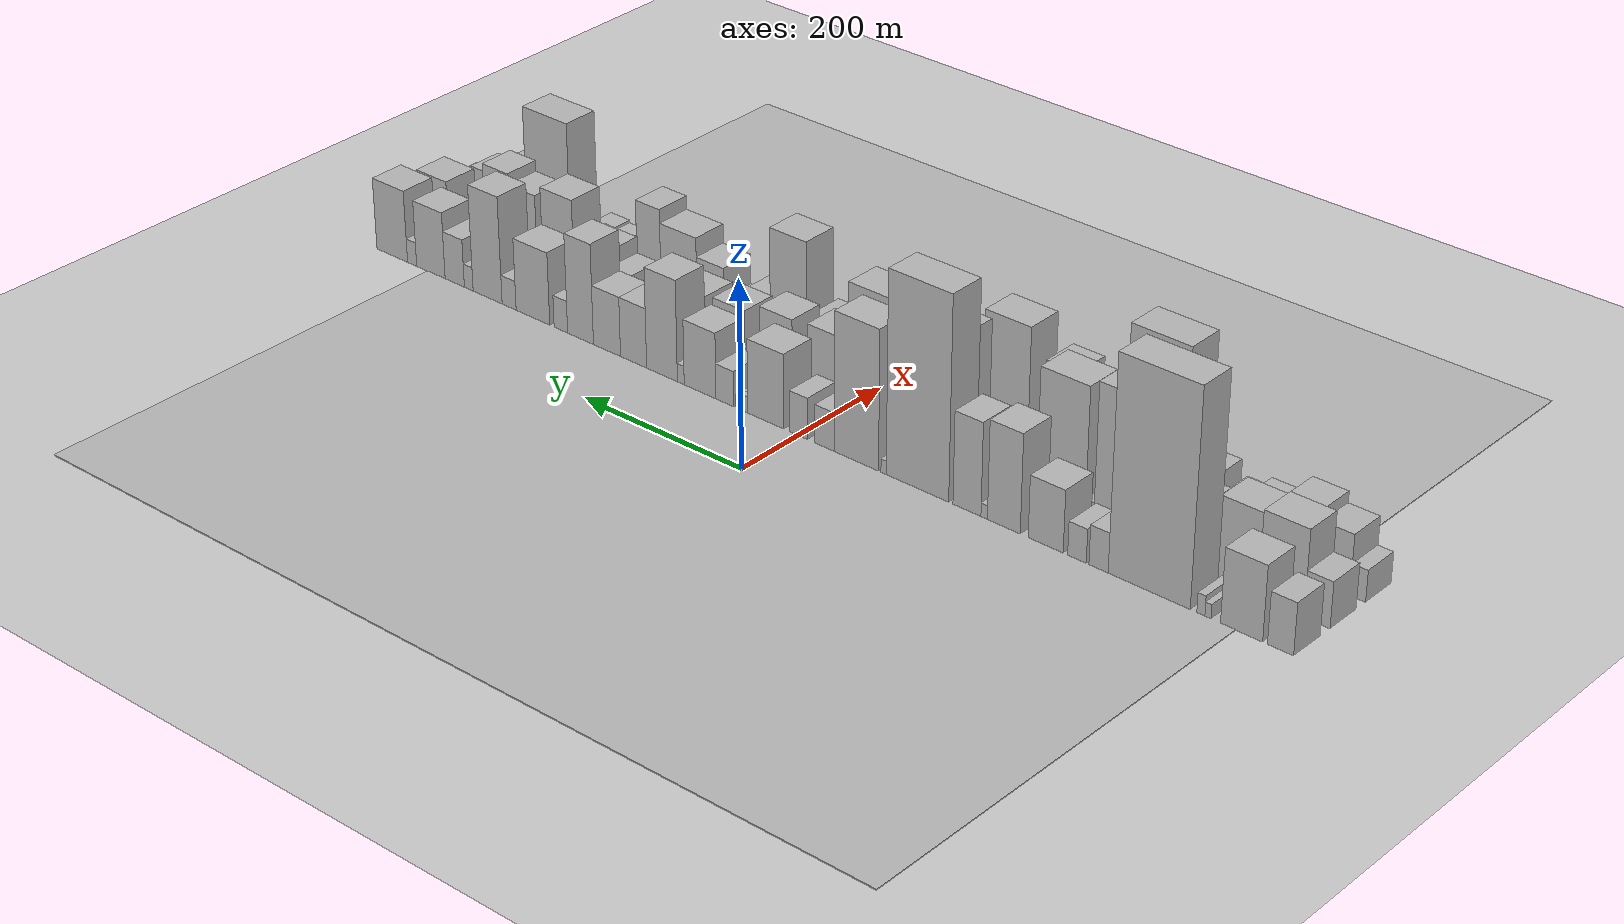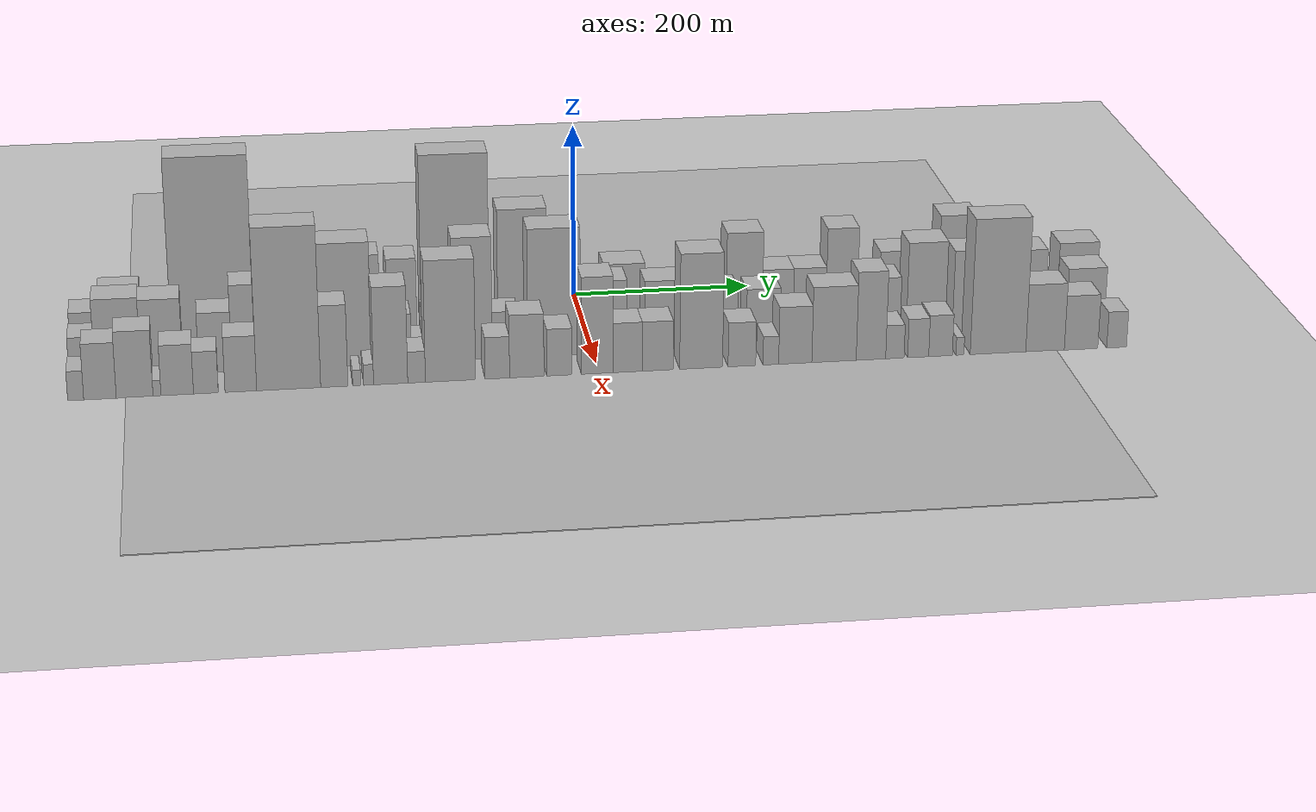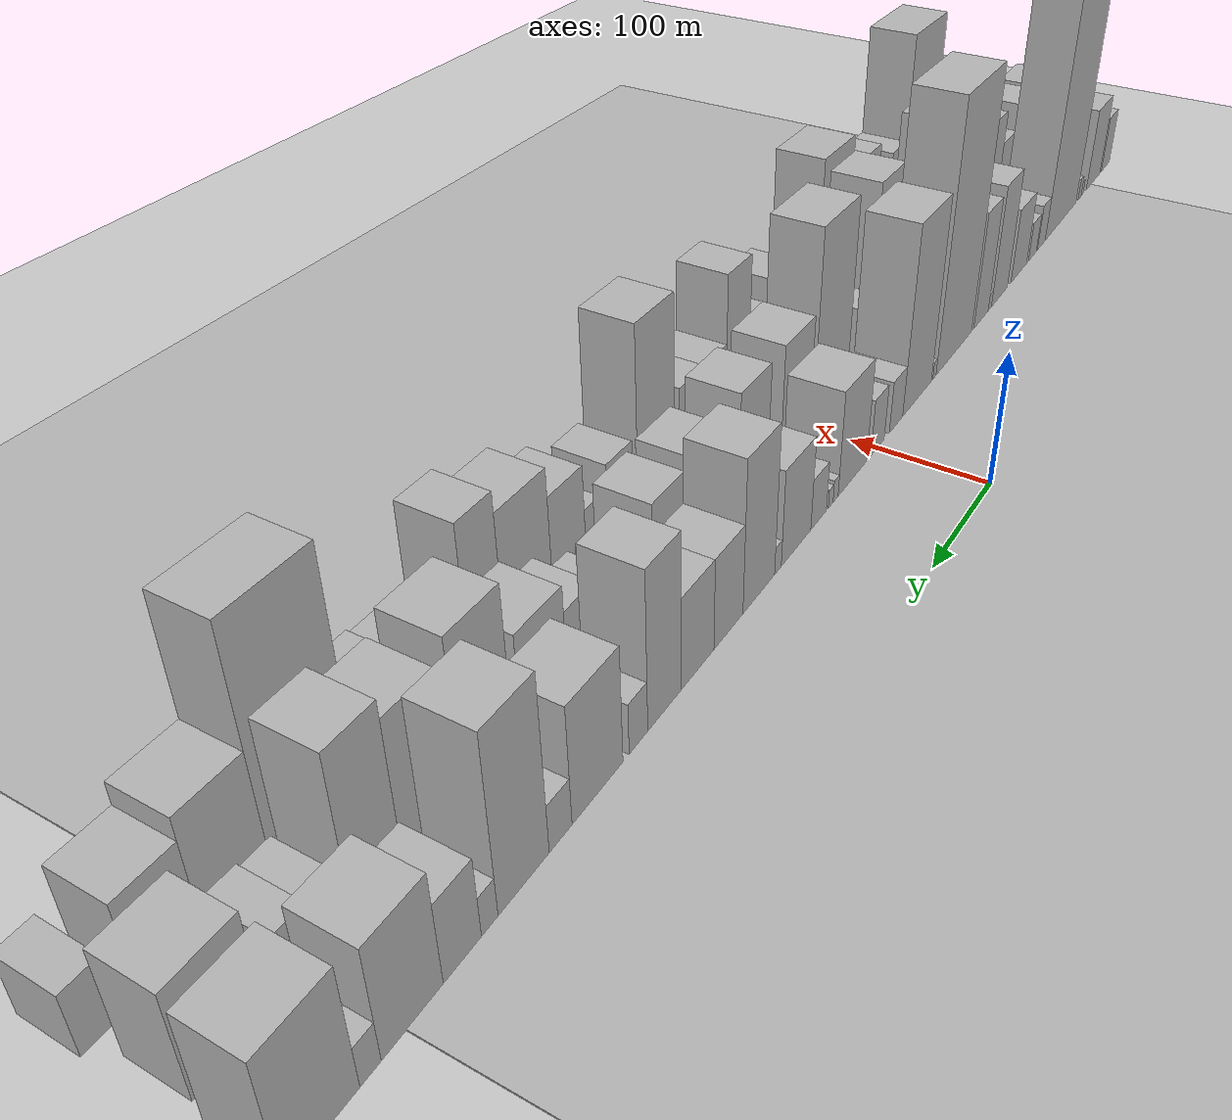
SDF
<?xml version="1.0" encoding="utf-8"?>

<sdf version="1.6">

   <world name="default">

      <gui fullscreen="0">

         <camera name="user_camera">

            <pose>-15 0 4.57585 0 0 0</pose>

            <view_controller>orbit</view_controller>

         </camera>

      </gui>

      <scene>

         <sky>

           <clouds>

             <speed>12</speed>

           </clouds>

         </sky>

         <ambient>0.4 0.4 0.4 1</ambient>

         <background>0.7 0.7 0.7 1</background>

         <shadows>1</shadows>

      </scene>

      <gravity>0 0 -9.8066</gravity>

      <magnetic_field>6e-06 2.3e-05 -4.2e-05</magnetic_field>

      <physics default="0" name="default_physics" type="ode">

         <ode>

            <solver>

               <type>quick</type>

               <iters>10</iters>

               <sor>1.0</sor>

               <use_dynamic_moi_rescaling>0</use_dynamic_moi_rescaling>

            </solver>

            <constraints>

               <cfm>0</cfm>

               <erp>0.2</erp>

               <contact_max_correcting_vel>100</contact_max_correcting_vel>

               <contact_surface_layer>0.001</contact_surface_layer>

            </constraints>

         </ode>

         <max_step_size>0.004</max_step_size>

         <real_time_factor>1</real_time_factor>

         <real_time_update_rate>250</real_time_update_rate>

      </physics>

      <light name="sun" type="directional">

         <cast_shadows>1</cast_shadows>

         <pose>0 0 10 0 0 0</pose>

         <diffuse>0.8 0.8 0.8 1</diffuse>

         <specular>0.2 0.2 0.2 1</specular>

         <attenuation>

            <range>1000</range>

            <constant>0.9</constant>

            <linear>0.01</linear>

            <quadratic>0.001</quadratic>

         </attenuation>

         <direction>-0.5 0.1 -0.9</direction>

      </light>

      <include>

         <name>ground_plane_1</name>

         <uri>model://HANNAS_ground_plane</uri>

         <pose>0 0 0  0 0 0</pose>

      </include>

      <include>

         <name>ground_plane_2</name>

         <uri>model://HANNAS_ground_plane</uri>

         <pose>100 0 0  0 0 0</pose>

      </include>

      <model name="building_1">

         <static>1</static>

         <pose frame="">100.0000 -546.4827 0 0.000000 0.000000 0.000000</pose>

         <link name="link">

            <pose frame="">0 0 27.00 0 0 0</pose>

            <collision name="collision">

               <geometry>

                  <box>

                     <size>40.0000 27.0345 54.0000</size>

                  </box>

               </geometry>

               <max_contacts>10</max_contacts>

               <surface>

                  <contact>

                     <ode/>

                  </contact>

                  <bounce/>

                  <friction>

                     <torsional>

                        <ode/>

                     </torsional>

                     <ode/>

                  </friction>

               </surface>

            </collision>

            <visual name="visual">

               <cast_shadows>0</cast_shadows>

               <geometry>

                  <box>

                     <size>40.0000 27.0345 54.0000</size>

                  </box>

               </geometry>

               <material>

                  <script>

                     <uri>model://HANNAS_wall/materials/scripts</uri>

                     <uri>model://HANNAS_wall/materials/textures</uri>

                     <name>vrc/HANNAS_wall</name>

                  </script>

               </material>

            </visual>

            <self_collide>0</self_collide>

            <enable_wind>0</enable_wind>

            <kinematic>0</kinematic>

         </link>

      </model>

      <model name="building_2">

         <static>1</static>

         <pose frame="">100.0000 -505.8893 0 0.000000 0.000000 0.000000</pose>

         <link name="link">

            <pose frame="">0 0 39.00 0 0 0</pose>

            <collision name="collision">

               <geometry>

                  <box>

                     <size>40.0000 44.1524 78.0000</size>

                  </box>

               </geometry>

               <max_contacts>10</max_contacts>

               <surface>

                  <contact>

                     <ode/>

                  </contact>

                  <bounce/>

                  <friction>

                     <torsional>

                        <ode/>

                     </torsional>

                     <ode/>

                  </friction>

               </surface>

            </collision>

            <visual name="visual">

               <cast_shadows>0</cast_shadows>

               <geometry>

                  <box>

                     <size>40.0000 44.1524 78.0000</size>

                  </box>

               </geometry>

               <material>

                  <script>

                     <uri>model://HANNAS_wall/materials/scripts</uri>

                     <uri>model://HANNAS_wall/materials/textures</uri>

                     <name>vrc/HANNAS_wall</name>

                  </script>

               </material>

            </visual>

            <self_collide>0</self_collide>

            <enable_wind>0</enable_wind>

            <kinematic>0</kinematic>

         </link>

      </model>

      <model name="building_3">

         <static>1</static>

         <pose frame="">100.0000 -470.5496 0 0.000000 0.000000 0.000000</pose>

         <link name="link">

            <pose frame="">0 0 7.50 0 0 0</pose>

            <collision name="collision">

               <geometry>

                  <box>

                     <size>40.0000 6.5270 15.0000</size>

                  </box>

               </geometry>

               <max_contacts>10</max_contacts>

               <surface>

                  <contact>

                     <ode/>

                  </contact>

                  <bounce/>

                  <friction>

                     <torsional>

                        <ode/>

                     </torsional>

                     <ode/>

                  </friction>

               </surface>

            </collision>

            <visual name="visual">

               <cast_shadows>0</cast_shadows>

               <geometry>

                  <box>

                     <size>40.0000 6.5270 15.0000</size>

                  </box>

               </geometry>

               <material>

                  <script>

                     <uri>model://HANNAS_wall/materials/scripts</uri>

                     <uri>model://HANNAS_wall/materials/textures</uri>

                     <name>vrc/HANNAS_wall</name>

                  </script>

               </material>

            </visual>

            <self_collide>0</self_collide>

            <enable_wind>0</enable_wind>

            <kinematic>0</kinematic>

         </link>

      </model>

      <model name="building_4">

         <static>1</static>

         <pose frame="">100.0000 -462.9985 0 0.000000 0.000000 0.000000</pose>

         <link name="link">

            <pose frame="">0 0 10.50 0 0 0</pose>

            <collision name="collision">

               <geometry>

                  <box>

                     <size>40.0000 8.5751 21.0000</size>

                  </box>

               </geometry>

               <max_contacts>10</max_contacts>

               <surface>

                  <contact>

                     <ode/>

                  </contact>

                  <bounce/>

                  <friction>

                     <torsional>

                        <ode/>

                     </torsional>

                     <ode/>

                  </friction>

               </surface>

            </collision>

            <visual name="visual">

               <cast_shadows>0</cast_shadows>

               <geometry>

                  <box>

                     <size>40.0000 8.5751 21.0000</size>

                  </box>

               </geometry>

               <material>

                  <script>

                     <uri>model://HANNAS_wall/materials/scripts</uri>

                     <uri>model://HANNAS_wall/materials/textures</uri>

                     <name>vrc/HANNAS_wall</name>

                  </script>

               </material>

            </visual>

            <self_collide>0</self_collide>

            <enable_wind>0</enable_wind>

            <kinematic>0</kinematic>

         </link>

      </model>

      <model name="building_5">

         <static>1</static>

         <pose frame="">100.0000 -407.1625 0 0.000000 0.000000 0.000000</pose>

         <link name="link">

            <pose frame="">0 0 112.50 0 0 0</pose>

            <collision name="collision">

               <geometry>

                  <box>

                     <size>40.0000 89.0970 225.0000</size>

                  </box>

               </geometry>

               <max_contacts>10</max_contacts>

               <surface>

                  <contact>

                     <ode/>

                  </contact>

                  <bounce/>

                  <friction>

                     <torsional>

                        <ode/>

                     </torsional>

                     <ode/>

                  </friction>

               </surface>

            </collision>

            <visual name="visual">

               <cast_shadows>0</cast_shadows>

               <geometry>

                  <box>

                     <size>40.0000 89.0970 225.0000</size>

                  </box>

               </geometry>

               <material>

                  <script>

                     <uri>model://HANNAS_wall/materials/scripts</uri>

                     <uri>model://HANNAS_wall/materials/textures</uri>

                     <name>vrc/HANNAS_wall</name>

                  </script>

               </material>

            </visual>

            <self_collide>0</self_collide>

            <enable_wind>0</enable_wind>

            <kinematic>0</kinematic>

         </link>

      </model>

      <model name="building_6">

         <static>1</static>

         <pose frame="">100.0000 -352.0170 0 0.000000 0.000000 0.000000</pose>

         <link name="link">

            <pose frame="">0 0 21.00 0 0 0</pose>

            <collision name="collision">

               <geometry>

                  <box>

                     <size>40.0000 21.1940 42.0000</size>

                  </box>

               </geometry>

               <max_contacts>10</max_contacts>

               <surface>

                  <contact>

                     <ode/>

                  </contact>

                  <bounce/>

                  <friction>

                     <torsional>

                        <ode/>

                     </torsional>

                     <ode/>

                  </friction>

               </surface>

            </collision>

            <visual name="visual">

               <cast_shadows>0</cast_shadows>

               <geometry>

                  <box>

                     <size>40.0000 21.1940 42.0000</size>

                  </box>

               </geometry>

               <material>

                  <script>

                     <uri>model://HANNAS_wall/materials/scripts</uri>

                     <uri>model://HANNAS_wall/materials/textures</uri>

                     <name>vrc/HANNAS_wall</name>

                  </script>

               </material>

            </visual>

            <self_collide>0</self_collide>

            <enable_wind>0</enable_wind>

            <kinematic>0</kinematic>

         </link>

      </model>

      <model name="building_7">

         <static>1</static>

         <pose frame="">100.0000 -328.0672 0 0.000000 0.000000 0.000000</pose>

         <link name="link">

            <pose frame="">0 0 18.00 0 0 0</pose>

            <collision name="collision">

               <geometry>

                  <box>

                     <size>40.0000 20.7055 36.0000</size>

                  </box>

               </geometry>

               <max_contacts>10</max_contacts>

               <surface>

                  <contact>

                     <ode/>

                  </contact>

                  <bounce/>

                  <friction>

                     <torsional>

                        <ode/>

                     </torsional>

                     <ode/>

                  </friction>

               </surface>

            </collision>

            <visual name="visual">

               <cast_shadows>0</cast_shadows>

               <geometry>

                  <box>

                     <size>40.0000 20.7055 36.0000</size>

                  </box>

               </geometry>

               <material>

                  <script>

                     <uri>model://HANNAS_wall/materials/scripts</uri>

                     <uri>model://HANNAS_wall/materials/textures</uri>

                     <name>vrc/HANNAS_wall</name>

                  </script>

               </material>

            </visual>

            <self_collide>0</self_collide>

            <enable_wind>0</enable_wind>

            <kinematic>0</kinematic>

         </link>

      </model>

      <model name="building_8">

         <static>1</static>

         <pose frame="">100.0000 -292.9577 0 0.000000 0.000000 0.000000</pose>

         <link name="link">

            <pose frame="">0 0 33.00 0 0 0</pose>

            <collision name="collision">

               <geometry>

                  <box>

                     <size>40.0000 39.5136 66.0000</size>

                  </box>

               </geometry>

               <max_contacts>10</max_contacts>

               <surface>

                  <contact>

                     <ode/>

                  </contact>

                  <bounce/>

                  <friction>

                     <torsional>

                        <ode/>

                     </torsional>

                     <ode/>

                  </friction>

               </surface>

            </collision>

            <visual name="visual">

               <cast_shadows>0</cast_shadows>

               <geometry>

                  <box>

                     <size>40.0000 39.5136 66.0000</size>

                  </box>

               </geometry>

               <material>

                  <script>

                     <uri>model://HANNAS_wall/materials/scripts</uri>

                     <uri>model://HANNAS_wall/materials/textures</uri>

                     <name>vrc/HANNAS_wall</name>

                  </script>

               </material>

            </visual>

            <self_collide>0</self_collide>

            <enable_wind>0</enable_wind>

            <kinematic>0</kinematic>

         </link>

      </model>

      <model name="building_9">

         <static>1</static>

         <pose frame="">100.0000 -245.3220 0 0.000000 0.000000 0.000000</pose>

         <link name="link">

            <pose frame="">0 0 52.50 0 0 0</pose>

            <collision name="collision">

               <geometry>

                  <box>

                     <size>40.0000 37.7578 105.0000</size>

                  </box>

               </geometry>

               <max_contacts>10</max_contacts>

               <surface>

                  <contact>

                     <ode/>

                  </contact>

                  <bounce/>

                  <friction>

                     <torsional>

                        <ode/>

                     </torsional>

                     <ode/>

                  </friction>

               </surface>

            </collision>

            <visual name="visual">

               <cast_shadows>0</cast_shadows>

               <geometry>

                  <box>

                     <size>40.0000 37.7578 105.0000</size>

                  </box>

               </geometry>

               <material>

                  <script>

                     <uri>model://HANNAS_wall/materials/scripts</uri>

                     <uri>model://HANNAS_wall/materials/textures</uri>

                     <name>vrc/HANNAS_wall</name>

                  </script>

               </material>

            </visual>

            <self_collide>0</self_collide>

            <enable_wind>0</enable_wind>

            <kinematic>0</kinematic>

         </link>

      </model>

      <model name="building_10">

         <static>1</static>

         <pose frame="">100.0000 -222.7115 0 0.000000 0.000000 0.000000</pose>

         <link name="link">

            <pose frame="">0 0 7.50 0 0 0</pose>

            <collision name="collision">

               <geometry>

                  <box>

                     <size>40.0000 7.4633 15.0000</size>

                  </box>

               </geometry>

               <max_contacts>10</max_contacts>

               <surface>

                  <contact>

                     <ode/>

                  </contact>

                  <bounce/>

                  <friction>

                     <torsional>

                        <ode/>

                     </torsional>

                     <ode/>

                  </friction>

               </surface>

            </collision>

            <visual name="visual">

               <cast_shadows>0</cast_shadows>

               <geometry>

                  <box>

                     <size>40.0000 7.4633 15.0000</size>

                  </box>

               </geometry>

               <material>

                  <script>

                     <uri>model://HANNAS_wall/materials/scripts</uri>

                     <uri>model://HANNAS_wall/materials/textures</uri>

                     <name>vrc/HANNAS_wall</name>

                  </script>

               </material>

            </visual>

            <self_collide>0</self_collide>

            <enable_wind>0</enable_wind>

            <kinematic>0</kinematic>

         </link>

      </model>

      <model name="building_11">

         <static>1</static>

         <pose frame="">100.0000 -202.6942 0 0.000000 0.000000 0.000000</pose>

         <link name="link">

            <pose frame="">0 0 49.50 0 0 0</pose>

            <collision name="collision">

               <geometry>

                  <box>

                     <size>40.0000 32.5713 99.0000</size>

                  </box>

               </geometry>

               <max_contacts>10</max_contacts>

               <surface>

                  <contact>

                     <ode/>

                  </contact>

                  <bounce/>

                  <friction>

                     <torsional>

                        <ode/>

                     </torsional>

                     <ode/>

                  </friction>

               </surface>

            </collision>

            <visual name="visual">

               <cast_shadows>0</cast_shadows>

               <geometry>

                  <box>

                     <size>40.0000 32.5713 99.0000</size>

                  </box>

               </geometry>

               <material>

                  <script>

                     <uri>model://HANNAS_wall/materials/scripts</uri>

                     <uri>model://HANNAS_wall/materials/textures</uri>

                     <name>vrc/HANNAS_wall</name>

                  </script>

               </material>

            </visual>

            <self_collide>0</self_collide>

            <enable_wind>0</enable_wind>

            <kinematic>0</kinematic>

         </link>

      </model>

      <model name="building_12">

         <static>1</static>

         <pose frame="">100.0000 -144.2849 0 0.000000 0.000000 0.000000</pose>

         <link name="link">

            <pose frame="">0 0 108.00 0 0 0</pose>

            <collision name="collision">

               <geometry>

                  <box>

                     <size>40.0000 74.2475 216.0000</size>

                  </box>

               </geometry>

               <max_contacts>10</max_contacts>

               <surface>

                  <contact>

                     <ode/>

                  </contact>

                  <bounce/>

                  <friction>

                     <torsional>

                        <ode/>

                     </torsional>

                     <ode/>

                  </friction>

               </surface>

            </collision>

            <visual name="visual">

               <cast_shadows>0</cast_shadows>

               <geometry>

                  <box>

                     <size>40.0000 74.2475 216.0000</size>

                  </box>

               </geometry>

               <material>

                  <script>

                     <uri>model://HANNAS_wall/materials/scripts</uri>

                     <uri>model://HANNAS_wall/materials/textures</uri>

                     <name>vrc/HANNAS_wall</name>

                  </script>

               </material>

            </visual>

            <self_collide>0</self_collide>

            <enable_wind>0</enable_wind>

            <kinematic>0</kinematic>

         </link>

      </model>

      <model name="building_13">

         <static>1</static>

         <pose frame="">100.0000 -104.0315 0 0.000000 0.000000 0.000000</pose>

         <link name="link">

            <pose frame="">0 0 7.50 0 0 0</pose>

            <collision name="collision">

               <geometry>

                  <box>

                     <size>40.0000 6.2592 15.0000</size>

                  </box>

               </geometry>

               <max_contacts>10</max_contacts>

               <surface>

                  <contact>

                     <ode/>

                  </contact>

                  <bounce/>

                  <friction>

                     <torsional>

                        <ode/>

                     </torsional>

                     <ode/>

                  </friction>

               </surface>

            </collision>

            <visual name="visual">

               <cast_shadows>0</cast_shadows>

               <geometry>

                  <box>

                     <size>40.0000 6.2592 15.0000</size>

                  </box>

               </geometry>

               <material>

                  <script>

                     <uri>model://HANNAS_wall/materials/scripts</uri>

                     <uri>model://HANNAS_wall/materials/textures</uri>

                     <name>vrc/HANNAS_wall</name>

                  </script>

               </material>

            </visual>

            <self_collide>0</self_collide>

            <enable_wind>0</enable_wind>

            <kinematic>0</kinematic>

         </link>

      </model>

      <model name="building_14">

         <static>1</static>

         <pose frame="">100.0000 -70.8796 0 0.000000 0.000000 0.000000</pose>

         <link name="link">

            <pose frame="">0 0 75.00 0 0 0</pose>

            <collision name="collision">

               <geometry>

                  <box>

                     <size>40.0000 54.0445 150.0000</size>

                  </box>

               </geometry>

               <max_contacts>10</max_contacts>

               <surface>

                  <contact>

                     <ode/>

                  </contact>

                  <bounce/>

                  <friction>

                     <torsional>

                        <ode/>

                     </torsional>

                     <ode/>

                  </friction>

               </surface>

            </collision>

            <visual name="visual">

               <cast_shadows>0</cast_shadows>

               <geometry>

                  <box>

                     <size>40.0000 54.0445 150.0000</size>

                  </box>

               </geometry>

               <material>

                  <script>

                     <uri>model://HANNAS_wall/materials/scripts</uri>

                     <uri>model://HANNAS_wall/materials/textures</uri>

                     <name>vrc/HANNAS_wall</name>

                  </script>

               </material>

            </visual>

            <self_collide>0</self_collide>

            <enable_wind>0</enable_wind>

            <kinematic>0</kinematic>

         </link>

      </model>

      <model name="building_15">

         <static>1</static>

         <pose frame="">100.0000 -31.9714 0 0.000000 0.000000 0.000000</pose>

         <link name="link">

            <pose frame="">0 0 21.00 0 0 0</pose>

            <collision name="collision">

               <geometry>

                  <box>

                     <size>40.0000 23.7720 42.0000</size>

                  </box>

               </geometry>

               <max_contacts>10</max_contacts>

               <surface>

                  <contact>

                     <ode/>

                  </contact>

                  <bounce/>

                  <friction>

                     <torsional>

                        <ode/>

                     </torsional>

                     <ode/>

                  </friction>

               </surface>

            </collision>

            <visual name="visual">

               <cast_shadows>0</cast_shadows>

               <geometry>

                  <box>

                     <size>40.0000 23.7720 42.0000</size>

                  </box>

               </geometry>

               <material>

                  <script>

                     <uri>model://HANNAS_wall/materials/scripts</uri>

                     <uri>model://HANNAS_wall/materials/textures</uri>

                     <name>vrc/HANNAS_wall</name>

                  </script>

               </material>

            </visual>

            <self_collide>0</self_collide>

            <enable_wind>0</enable_wind>

            <kinematic>0</kinematic>

         </link>

      </model>

      <model name="building_16">

         <static>1</static>

         <pose frame="">100.0000 0.2246 0 0.000000 0.000000 0.000000</pose>

         <link name="link">

            <pose frame="">0 0 22.50 0 0 0</pose>

            <collision name="collision">

               <geometry>

                  <box>

                     <size>40.0000 22.6201 45.0000</size>

                  </box>

               </geometry>

               <max_contacts>10</max_contacts>

               <surface>

                  <contact>

                     <ode/>

                  </contact>

                  <bounce/>

                  <friction>

                     <torsional>

                        <ode/>

                     </torsional>

                     <ode/>

                  </friction>

               </surface>

            </collision>

            <visual name="visual">

               <cast_shadows>0</cast_shadows>

               <geometry>

                  <box>

                     <size>40.0000 22.6201 45.0000</size>

                  </box>

               </geometry>

               <material>

                  <script>

                     <uri>model://HANNAS_wall/materials/scripts</uri>

                     <uri>model://HANNAS_wall/materials/textures</uri>

                     <name>vrc/HANNAS_wall</name>

                  </script>

               </material>

            </visual>

            <self_collide>0</self_collide>

            <enable_wind>0</enable_wind>

            <kinematic>0</kinematic>

         </link>

      </model>

      <model name="building_17">

         <static>1</static>

         <pose frame="">100.0000 41.3504 0 0.000000 0.000000 0.000000</pose>

         <link name="link">

            <pose frame="">0 0 40.50 0 0 0</pose>

            <collision name="collision">

               <geometry>

                  <box>

                     <size>40.0000 45.6313 81.0000</size>

                  </box>

               </geometry>

               <max_contacts>10</max_contacts>

               <surface>

                  <contact>

                     <ode/>

                  </contact>

                  <bounce/>

                  <friction>

                     <torsional>

                        <ode/>

                     </torsional>

                     <ode/>

                  </friction>

               </surface>

            </collision>

            <visual name="visual">

               <cast_shadows>0</cast_shadows>

               <geometry>

                  <box>

                     <size>40.0000 45.6313 81.0000</size>

                  </box>

               </geometry>

               <material>

                  <script>

                     <uri>model://HANNAS_wall/materials/scripts</uri>

                     <uri>model://HANNAS_wall/materials/textures</uri>

                     <name>vrc/HANNAS_wall</name>

                  </script>

               </material>

            </visual>

            <self_collide>0</self_collide>

            <enable_wind>0</enable_wind>

            <kinematic>0</kinematic>

         </link>

      </model>

      <model name="building_18">

         <static>1</static>

         <pose frame="">100.0000 67.9981 0 0.000000 0.000000 0.000000</pose>

         <link name="link">

            <pose frame="">0 0 9.00 0 0 0</pose>

            <collision name="collision">

               <geometry>

                  <box>

                     <size>40.0000 7.6641 18.0000</size>

                  </box>

               </geometry>

               <max_contacts>10</max_contacts>

               <surface>

                  <contact>

                     <ode/>

                  </contact>

                  <bounce/>

                  <friction>

                     <torsional>

                        <ode/>

                     </torsional>

                     <ode/>

                  </friction>

               </surface>

            </collision>

            <visual name="visual">

               <cast_shadows>0</cast_shadows>

               <geometry>

                  <box>

                     <size>40.0000 7.6641 18.0000</size>

                  </box>

               </geometry>

               <material>

                  <script>

                     <uri>model://HANNAS_wall/materials/scripts</uri>

                     <uri>model://HANNAS_wall/materials/textures</uri>

                     <name>vrc/HANNAS_wall</name>

                  </script>

               </material>

            </visual>

            <self_collide>0</self_collide>

            <enable_wind>0</enable_wind>

            <kinematic>0</kinematic>

         </link>

      </model>

      <model name="building_19">

         <static>1</static>

         <pose frame="">100.0000 75.4089 0 0.000000 0.000000 0.000000</pose>

         <link name="link">

            <pose frame="">0 0 7.50 0 0 0</pose>

            <collision name="collision">

               <geometry>

                  <box>

                     <size>40.0000 7.1576 15.0000</size>

                  </box>

               </geometry>

               <max_contacts>10</max_contacts>

               <surface>

                  <contact>

                     <ode/>

                  </contact>

                  <bounce/>

                  <friction>

                     <torsional>

                        <ode/>

                     </torsional>

                     <ode/>

                  </friction>

               </surface>

            </collision>

            <visual name="visual">

               <cast_shadows>0</cast_shadows>

               <geometry>

                  <box>

                     <size>40.0000 7.1576 15.0000</size>

                  </box>

               </geometry>

               <material>

                  <script>

                     <uri>model://HANNAS_wall/materials/scripts</uri>

                     <uri>model://HANNAS_wall/materials/textures</uri>

                     <name>vrc/HANNAS_wall</name>

                  </script>

               </material>

            </visual>

            <self_collide>0</self_collide>

            <enable_wind>0</enable_wind>

            <kinematic>0</kinematic>

         </link>

      </model>

      <model name="building_20">

         <static>1</static>

         <pose frame="">100.0000 93.3953 0 0.000000 0.000000 0.000000</pose>

         <link name="link">

            <pose frame="">0 0 19.50 0 0 0</pose>

            <collision name="collision">

               <geometry>

                  <box>

                     <size>40.0000 22.8153 39.0000</size>

                  </box>

               </geometry>

               <max_contacts>10</max_contacts>

               <surface>

                  <contact>

                     <ode/>

                  </contact>

                  <bounce/>

                  <friction>

                     <torsional>

                        <ode/>

                     </torsional>

                     <ode/>

                  </friction>

               </surface>

            </collision>

            <visual name="visual">

               <cast_shadows>0</cast_shadows>

               <geometry>

                  <box>

                     <size>40.0000 22.8153 39.0000</size>

                  </box>

               </geometry>

               <material>

                  <script>

                     <uri>model://HANNAS_wall/materials/scripts</uri>

                     <uri>model://HANNAS_wall/materials/textures</uri>

                     <name>vrc/HANNAS_wall</name>

                  </script>

               </material>

            </visual>

            <self_collide>0</self_collide>

            <enable_wind>0</enable_wind>

            <kinematic>0</kinematic>

         </link>

      </model>

      <model name="building_21">

         <static>1</static>

         <pose frame="">100.0000 125.3801 0 0.000000 0.000000 0.000000</pose>

         <link name="link">

            <pose frame="">0 0 36.00 0 0 0</pose>

            <collision name="collision">

               <geometry>

                  <box>

                     <size>40.0000 41.1543 72.0000</size>

                  </box>

               </geometry>

               <max_contacts>10</max_contacts>

               <surface>

                  <contact>

                     <ode/>

                  </contact>

                  <bounce/>

                  <friction>

                     <torsional>

                        <ode/>

                     </torsional>

                     <ode/>

                  </friction>

               </surface>

            </collision>

            <visual name="visual">

               <cast_shadows>0</cast_shadows>

               <geometry>

                  <box>

                     <size>40.0000 41.1543 72.0000</size>

                  </box>

               </geometry>

               <material>

                  <script>

                     <uri>model://HANNAS_wall/materials/scripts</uri>

                     <uri>model://HANNAS_wall/materials/textures</uri>

                     <name>vrc/HANNAS_wall</name>

                  </script>

               </material>

            </visual>

            <self_collide>0</self_collide>

            <enable_wind>0</enable_wind>

            <kinematic>0</kinematic>

         </link>

      </model>

      <model name="building_22">

         <static>1</static>

         <pose frame="">100.0000 150.4188 0 0.000000 0.000000 0.000000</pose>

         <link name="link">

            <pose frame="">0 0 10.50 0 0 0</pose>

            <collision name="collision">

               <geometry>

                  <box>

                     <size>40.0000 8.9230 21.0000</size>

                  </box>

               </geometry>

               <max_contacts>10</max_contacts>

               <surface>

                  <contact>

                     <ode/>

                  </contact>

                  <bounce/>

                  <friction>

                     <torsional>

                        <ode/>

                     </torsional>

                     <ode/>

                  </friction>

               </surface>

            </collision>

            <visual name="visual">

               <cast_shadows>0</cast_shadows>

               <geometry>

                  <box>

                     <size>40.0000 8.9230 21.0000</size>

                  </box>

               </geometry>

               <material>

                  <script>

                     <uri>model://HANNAS_wall/materials/scripts</uri>

                     <uri>model://HANNAS_wall/materials/textures</uri>

                     <name>vrc/HANNAS_wall</name>

                  </script>

               </material>

            </visual>

            <self_collide>0</self_collide>

            <enable_wind>0</enable_wind>

            <kinematic>0</kinematic>

         </link>

      </model>

      <model name="building_23">

         <static>1</static>

         <pose frame="">100.0000 175.1559 0 0.000000 0.000000 0.000000</pose>

         <link name="link">

            <pose frame="">0 0 55.50 0 0 0</pose>

            <collision name="collision">

               <geometry>

                  <box>

                     <size>40.0000 40.5513 111.0000</size>

                  </box>

               </geometry>

               <max_contacts>10</max_contacts>

               <surface>

                  <contact>

                     <ode/>

                  </contact>

                  <bounce/>

                  <friction>

                     <torsional>

                        <ode/>

                     </torsional>

                     <ode/>

                  </friction>

               </surface>

            </collision>

            <visual name="visual">

               <cast_shadows>0</cast_shadows>

               <geometry>

                  <box>

                     <size>40.0000 40.5513 111.0000</size>

                  </box>

               </geometry>

               <material>

                  <script>

                     <uri>model://HANNAS_wall/materials/scripts</uri>

                     <uri>model://HANNAS_wall/materials/textures</uri>

                     <name>vrc/HANNAS_wall</name>

                  </script>

               </material>

            </visual>

            <self_collide>0</self_collide>

            <enable_wind>0</enable_wind>

            <kinematic>0</kinematic>

         </link>

      </model>

      <model name="building_24">

         <static>1</static>

         <pose frame="">100.0000 212.8494 0 0.000000 0.000000 0.000000</pose>

         <link name="link">

            <pose frame="">0 0 33.00 0 0 0</pose>

            <collision name="collision">

               <geometry>

                  <box>

                     <size>40.0000 34.8357 66.0000</size>

                  </box>

               </geometry>

               <max_contacts>10</max_contacts>

               <surface>

                  <contact>

                     <ode/>

                  </contact>

                  <bounce/>

                  <friction>

                     <torsional>

                        <ode/>

                     </torsional>

                     <ode/>

                  </friction>

               </surface>

            </collision>

            <visual name="visual">

               <cast_shadows>0</cast_shadows>

               <geometry>

                  <box>

                     <size>40.0000 34.8357 66.0000</size>

                  </box>

               </geometry>

               <material>

                  <script>

                     <uri>model://HANNAS_wall/materials/scripts</uri>

                     <uri>model://HANNAS_wall/materials/textures</uri>

                     <name>vrc/HANNAS_wall</name>

                  </script>

               </material>

            </visual>

            <self_collide>0</self_collide>

            <enable_wind>0</enable_wind>

            <kinematic>0</kinematic>

         </link>

      </model>

      <model name="building_25">

         <static>1</static>

         <pose frame="">100.0000 248.5443 0 0.000000 0.000000 0.000000</pose>

         <link name="link">

            <pose frame="">0 0 33.00 0 0 0</pose>

            <collision name="collision">

               <geometry>

                  <box>

                     <size>40.0000 36.5541 66.0000</size>

                  </box>

               </geometry>

               <max_contacts>10</max_contacts>

               <surface>

                  <contact>

                     <ode/>

                  </contact>

                  <bounce/>

                  <friction>

                     <torsional>

                        <ode/>

                     </torsional>

                     <ode/>

                  </friction>

               </surface>

            </collision>

            <visual name="visual">

               <cast_shadows>0</cast_shadows>

               <geometry>

                  <box>

                     <size>40.0000 36.5541 66.0000</size>

                  </box>

               </geometry>

               <material>

                  <script>

                     <uri>model://HANNAS_wall/materials/scripts</uri>

                     <uri>model://HANNAS_wall/materials/textures</uri>

                     <name>vrc/HANNAS_wall</name>

                  </script>

               </material>

            </visual>

            <self_collide>0</self_collide>

            <enable_wind>0</enable_wind>

            <kinematic>0</kinematic>

         </link>

      </model>

      <model name="building_26">

         <static>1</static>

         <pose frame="">100.0000 284.4584 0 0.000000 0.000000 0.000000</pose>

         <link name="link">

            <pose frame="">0 0 55.50 0 0 0</pose>

            <collision name="collision">

               <geometry>

                  <box>

                     <size>40.0000 35.2741 111.0000</size>

                  </box>

               </geometry>

               <max_contacts>10</max_contacts>

               <surface>

                  <contact>

                     <ode/>

                  </contact>

                  <bounce/>

                  <friction>

                     <torsional>

                        <ode/>

                     </torsional>

                     <ode/>

                  </friction>

               </surface>

            </collision>

            <visual name="visual">

               <cast_shadows>0</cast_shadows>

               <geometry>

                  <box>

                     <size>40.0000 35.2741 111.0000</size>

                  </box>

               </geometry>

               <material>

                  <script>

                     <uri>model://HANNAS_wall/materials/scripts</uri>

                     <uri>model://HANNAS_wall/materials/textures</uri>

                     <name>vrc/HANNAS_wall</name>

                  </script>

               </material>

            </visual>

            <self_collide>0</self_collide>

            <enable_wind>0</enable_wind>

            <kinematic>0</kinematic>

         </link>

      </model>

      <model name="building_27">

         <static>1</static>

         <pose frame="">100.0000 311.3756 0 0.000000 0.000000 0.000000</pose>

         <link name="link">

            <pose frame="">0 0 18.00 0 0 0</pose>

            <collision name="collision">

               <geometry>

                  <box>

                     <size>40.0000 18.5601 36.0000</size>

                  </box>

               </geometry>

               <max_contacts>10</max_contacts>

               <surface>

                  <contact>

                     <ode/>

                  </contact>

                  <bounce/>

                  <friction>

                     <torsional>

                        <ode/>

                     </torsional>

                     <ode/>

                  </friction>

               </surface>

            </collision>

            <visual name="visual">

               <cast_shadows>0</cast_shadows>

               <geometry>

                  <box>

                     <size>40.0000 18.5601 36.0000</size>

                  </box>

               </geometry>

               <material>

                  <script>

                     <uri>model://HANNAS_wall/materials/scripts</uri>

                     <uri>model://HANNAS_wall/materials/textures</uri>

                     <name>vrc/HANNAS_wall</name>

                  </script>

               </material>

            </visual>

            <self_collide>0</self_collide>

            <enable_wind>0</enable_wind>

            <kinematic>0</kinematic>

         </link>

      </model>

      <model name="building_28">

         <static>1</static>

         <pose frame="">100.0000 350.1143 0 0.000000 0.000000 0.000000</pose>

         <link name="link">

            <pose frame="">0 0 40.50 0 0 0</pose>

            <collision name="collision">

               <geometry>

                  <box>

                     <size>40.0000 46.9174 81.0000</size>

                  </box>

               </geometry>

               <max_contacts>10</max_contacts>

               <surface>

                  <contact>

                     <ode/>

                  </contact>

                  <bounce/>

                  <friction>

                     <torsional>

                        <ode/>

                     </torsional>

                     <ode/>

                  </friction>

               </surface>

            </collision>

            <visual name="visual">

               <cast_shadows>0</cast_shadows>

               <geometry>

                  <box>

                     <size>40.0000 46.9174 81.0000</size>

                  </box>

               </geometry>

               <material>

                  <script>

                     <uri>model://HANNAS_wall/materials/scripts</uri>

                     <uri>model://HANNAS_wall/materials/textures</uri>

                     <name>vrc/HANNAS_wall</name>

                  </script>

               </material>

            </visual>

            <self_collide>0</self_collide>

            <enable_wind>0</enable_wind>

            <kinematic>0</kinematic>

         </link>

      </model>

      <model name="building_29">

         <static>1</static>

         <pose frame="">100.0000 383.4061 0 0.000000 0.000000 0.000000</pose>

         <link name="link">

            <pose frame="">0 0 16.50 0 0 0</pose>

            <collision name="collision">

               <geometry>

                  <box>

                     <size>40.0000 19.6661 33.0000</size>

                  </box>

               </geometry>

               <max_contacts>10</max_contacts>

               <surface>

                  <contact>

                     <ode/>

                  </contact>

                  <bounce/>

                  <friction>

                     <torsional>

                        <ode/>

                     </torsional>

                     <ode/>

                  </friction>

               </surface>

            </collision>

            <visual name="visual">

               <cast_shadows>0</cast_shadows>

               <geometry>

                  <box>

                     <size>40.0000 19.6661 33.0000</size>

                  </box>

               </geometry>

               <material>

                  <script>

                     <uri>model://HANNAS_wall/materials/scripts</uri>

                     <uri>model://HANNAS_wall/materials/textures</uri>

                     <name>vrc/HANNAS_wall</name>

                  </script>

               </material>

            </visual>

            <self_collide>0</self_collide>

            <enable_wind>0</enable_wind>

            <kinematic>0</kinematic>

         </link>

      </model>

      <model name="building_30">

         <static>1</static>

         <pose frame="">100.0000 413.8622 0 0.000000 0.000000 0.000000</pose>

         <link name="link">

            <pose frame="">0 0 60.00 0 0 0</pose>

            <collision name="collision">

               <geometry>

                  <box>

                     <size>40.0000 41.2460 120.0000</size>

                  </box>

               </geometry>

               <max_contacts>10</max_contacts>

               <surface>

                  <contact>

                     <ode/>

                  </contact>

                  <bounce/>

                  <friction>

                     <torsional>

                        <ode/>

                     </torsional>

                     <ode/>

                  </friction>

               </surface>

            </collision>

            <visual name="visual">

               <cast_shadows>0</cast_shadows>

               <geometry>

                  <box>

                     <size>40.0000 41.2460 120.0000</size>

                  </box>

               </geometry>

               <material>

                  <script>

                     <uri>model://HANNAS_wall/materials/scripts</uri>

                     <uri>model://HANNAS_wall/materials/textures</uri>

                     <name>vrc/HANNAS_wall</name>

                  </script>

               </material>

            </visual>

            <self_collide>0</self_collide>

            <enable_wind>0</enable_wind>

            <kinematic>0</kinematic>

         </link>

      </model>

      <model name="building_31">

         <static>1</static>

         <pose frame="">100.0000 440.7601 0 0.000000 0.000000 0.000000</pose>

         <link name="link">

            <pose frame="">0 0 13.50 0 0 0</pose>

            <collision name="collision">

               <geometry>

                  <box>

                     <size>40.0000 12.5497 27.0000</size>

                  </box>

               </geometry>

               <max_contacts>10</max_contacts>

               <surface>

                  <contact>

                     <ode/>

                  </contact>

                  <bounce/>

                  <friction>

                     <torsional>

                        <ode/>

                     </torsional>

                     <ode/>

                  </friction>

               </surface>

            </collision>

            <visual name="visual">

               <cast_shadows>0</cast_shadows>

               <geometry>

                  <box>

                     <size>40.0000 12.5497 27.0000</size>

                  </box>

               </geometry>

               <material>

                  <script>

                     <uri>model://HANNAS_wall/materials/scripts</uri>

                     <uri>model://HANNAS_wall/materials/textures</uri>

                     <name>vrc/HANNAS_wall</name>

                  </script>

               </material>

            </visual>

            <self_collide>0</self_collide>

            <enable_wind>0</enable_wind>

            <kinematic>0</kinematic>

         </link>

      </model>

      <model name="building_32">

         <static>1</static>

         <pose frame="">100.0000 460.9115 0 0.000000 0.000000 0.000000</pose>

         <link name="link">

            <pose frame="">0 0 27.00 0 0 0</pose>

            <collision name="collision">

               <geometry>

                  <box>

                     <size>40.0000 27.7532 54.0000</size>

                  </box>

               </geometry>

               <max_contacts>10</max_contacts>

               <surface>

                  <contact>

                     <ode/>

                  </contact>

                  <bounce/>

                  <friction>

                     <torsional>

                        <ode/>

                     </torsional>

                     <ode/>

                  </friction>

               </surface>

            </collision>

            <visual name="visual">

               <cast_shadows>0</cast_shadows>

               <geometry>

                  <box>

                     <size>40.0000 27.7532 54.0000</size>

                  </box>

               </geometry>

               <material>

                  <script>

                     <uri>model://HANNAS_wall/materials/scripts</uri>

                     <uri>model://HANNAS_wall/materials/textures</uri>

                     <name>vrc/HANNAS_wall</name>

                  </script>

               </material>

            </visual>

            <self_collide>0</self_collide>

            <enable_wind>0</enable_wind>

            <kinematic>0</kinematic>

         </link>

      </model>

      <model name="building_33">

         <static>1</static>

         <pose frame="">100.0000 495.5422 0 0.000000 0.000000 0.000000</pose>

         <link name="link">

            <pose frame="">0 0 37.50 0 0 0</pose>

            <collision name="collision">

               <geometry>

                  <box>

                     <size>40.0000 41.5080 75.0000</size>

                  </box>

               </geometry>

               <max_contacts>10</max_contacts>

               <surface>

                  <contact>

                     <ode/>

                  </contact>

                  <bounce/>

                  <friction>

                     <torsional>

                        <ode/>

                     </torsional>

                     <ode/>

                  </friction>

               </surface>

            </collision>

            <visual name="visual">

               <cast_shadows>0</cast_shadows>

               <geometry>

                  <box>

                     <size>40.0000 41.5080 75.0000</size>

                  </box>

               </geometry>

               <material>

                  <script>

                     <uri>model://HANNAS_wall/materials/scripts</uri>

                     <uri>model://HANNAS_wall/materials/textures</uri>

                     <name>vrc/HANNAS_wall</name>

                  </script>

               </material>

            </visual>

            <self_collide>0</self_collide>

            <enable_wind>0</enable_wind>

            <kinematic>0</kinematic>

         </link>

      </model>

      <model name="building_34">

         <static>1</static>

         <pose frame="">100.0000 522.9853 0 0.000000 0.000000 0.000000</pose>

         <link name="link">

            <pose frame="">0 0 13.50 0 0 0</pose>

            <collision name="collision">

               <geometry>

                  <box>

                     <size>40.0000 13.3782 27.0000</size>

                  </box>

               </geometry>

               <max_contacts>10</max_contacts>

               <surface>

                  <contact>

                     <ode/>

                  </contact>

                  <bounce/>

                  <friction>

                     <torsional>

                        <ode/>

                     </torsional>

                     <ode/>

                  </friction>

               </surface>

            </collision>

            <visual name="visual">

               <cast_shadows>0</cast_shadows>

               <geometry>

                  <box>

                     <size>40.0000 13.3782 27.0000</size>

                  </box>

               </geometry>

               <material>

                  <script>

                     <uri>model://HANNAS_wall/materials/scripts</uri>

                     <uri>model://HANNAS_wall/materials/textures</uri>

                     <name>vrc/HANNAS_wall</name>

                  </script>

               </material>

            </visual>

            <self_collide>0</self_collide>

            <enable_wind>0</enable_wind>

            <kinematic>0</kinematic>

         </link>

      </model>

      <model name="building_35">

         <static>1</static>

         <pose frame="">100.0000 552.3369 0 0.000000 0.000000 0.000000</pose>

         <link name="link">

            <pose frame="">0 0 40.50 0 0 0</pose>

            <collision name="collision">

               <geometry>

                  <box>

                     <size>40.0000 45.3250 81.0000</size>

                  </box>

               </geometry>

               <max_contacts>10</max_contacts>

               <surface>

                  <contact>

                     <ode/>

                  </contact>

                  <bounce/>

                  <friction>

                     <torsional>

                        <ode/>

                     </torsional>

                     <ode/>

                  </friction>

               </surface>

            </collision>

            <visual name="visual">

               <cast_shadows>0</cast_shadows>

               <geometry>

                  <box>

                     <size>40.0000 45.3250 81.0000</size>

                  </box>

               </geometry>

               <material>

                  <script>

                     <uri>model://HANNAS_wall/materials/scripts</uri>

                     <uri>model://HANNAS_wall/materials/textures</uri>

                     <name>vrc/HANNAS_wall</name>

                  </script>

               </material>

            </visual>

            <self_collide>0</self_collide>

            <enable_wind>0</enable_wind>

            <kinematic>0</kinematic>

         </link>

      </model>

      <model name="building_36">

         <static>1</static>

         <pose frame="">155.0000 -546.4578 0 0.000000 0.000000 0.000000</pose>

         <link name="link">

            <pose frame="">0 0 24.00 0 0 0</pose>

            <collision name="collision">

               <geometry>

                  <box>

                     <size>40.0000 27.0844 48.0000</size>

                  </box>

               </geometry>

               <max_contacts>10</max_contacts>

               <surface>

                  <contact>

                     <ode/>

                  </contact>

                  <bounce/>

                  <friction>

                     <torsional>

                        <ode/>

                     </torsional>

                     <ode/>

                  </friction>

               </surface>

            </collision>

            <visual name="visual">

               <cast_shadows>0</cast_shadows>

               <geometry>

                  <box>

                     <size>40.0000 27.0844 48.0000</size>

                  </box>

               </geometry>

               <material>

                  <script>

                     <uri>model://HANNAS_wall/materials/scripts</uri>

                     <uri>model://HANNAS_wall/materials/textures</uri>

                     <name>vrc/HANNAS_wall</name>

                  </script>

               </material>

            </visual>

            <self_collide>0</self_collide>

            <enable_wind>0</enable_wind>

            <kinematic>0</kinematic>

         </link>

      </model>

      <model name="building_37">

         <static>1</static>

         <pose frame="">155.0000 -508.7451 0 0.000000 0.000000 0.000000</pose>

         <link name="link">

            <pose frame="">0 0 45.00 0 0 0</pose>

            <collision name="collision">

               <geometry>

                  <box>

                     <size>40.0000 48.3409 90.0000</size>

                  </box>

               </geometry>

               <max_contacts>10</max_contacts>

               <surface>

                  <contact>

                     <ode/>

                  </contact>

                  <bounce/>

                  <friction>

                     <torsional>

                        <ode/>

                     </torsional>

                     <ode/>

                  </friction>

               </surface>

            </collision>

            <visual name="visual">

               <cast_shadows>0</cast_shadows>

               <geometry>

                  <box>

                     <size>40.0000 48.3409 90.0000</size>

                  </box>

               </geometry>

               <material>

                  <script>

                     <uri>model://HANNAS_wall/materials/scripts</uri>

                     <uri>model://HANNAS_wall/materials/textures</uri>

                     <name>vrc/HANNAS_wall</name>

                  </script>

               </material>

            </visual>

            <self_collide>0</self_collide>

            <enable_wind>0</enable_wind>

            <kinematic>0</kinematic>

         </link>

      </model>

      <model name="building_38">

         <static>1</static>

         <pose frame="">155.0000 -462.3962 0 0.000000 0.000000 0.000000</pose>

         <link name="link">

            <pose frame="">0 0 43.50 0 0 0</pose>

            <collision name="collision">

               <geometry>

                  <box>

                     <size>40.0000 44.3568 87.0000</size>

                  </box>

               </geometry>

               <max_contacts>10</max_contacts>

               <surface>

                  <contact>

                     <ode/>

                  </contact>

                  <bounce/>

                  <friction>

                     <torsional>

                        <ode/>

                     </torsional>

                     <ode/>

                  </friction>

               </surface>

            </collision>

            <visual name="visual">

               <cast_shadows>0</cast_shadows>

               <geometry>

                  <box>

                     <size>40.0000 44.3568 87.0000</size>

                  </box>

               </geometry>

               <material>

                  <script>

                     <uri>model://HANNAS_wall/materials/scripts</uri>

                     <uri>model://HANNAS_wall/materials/textures</uri>

                     <name>vrc/HANNAS_wall</name>

                  </script>

               </material>

            </visual>

            <self_collide>0</self_collide>

            <enable_wind>0</enable_wind>

            <kinematic>0</kinematic>

         </link>

      </model>

      <model name="building_39">

         <static>1</static>

         <pose frame="">155.0000 -431.8418 0 0.000000 0.000000 0.000000</pose>

         <link name="link">

            <pose frame="">0 0 9.00 0 0 0</pose>

            <collision name="collision">

               <geometry>

                  <box>

                     <size>40.0000 8.7520 18.0000</size>

                  </box>

               </geometry>

               <max_contacts>10</max_contacts>

               <surface>

                  <contact>

                     <ode/>

                  </contact>

                  <bounce/>

                  <friction>

                     <torsional>

                        <ode/>

                     </torsional>

                     <ode/>

                  </friction>

               </surface>

            </collision>

            <visual name="visual">

               <cast_shadows>0</cast_shadows>

               <geometry>

                  <box>

                     <size>40.0000 8.7520 18.0000</size>

                  </box>

               </geometry>

               <material>

                  <script>

                     <uri>model://HANNAS_wall/materials/scripts</uri>

                     <uri>model://HANNAS_wall/materials/textures</uri>

                     <name>vrc/HANNAS_wall</name>

                  </script>

               </material>

            </visual>

            <self_collide>0</self_collide>

            <enable_wind>0</enable_wind>

            <kinematic>0</kinematic>

         </link>

      </model>

      <model name="building_40">

         <static>1</static>

         <pose frame="">155.0000 -405.9061 0 0.000000 0.000000 0.000000</pose>

         <link name="link">

            <pose frame="">0 0 34.50 0 0 0</pose>

            <collision name="collision">

               <geometry>

                  <box>

                     <size>40.0000 35.1195 69.0000</size>

                  </box>

               </geometry>

               <max_contacts>10</max_contacts>

               <surface>

                  <contact>

                     <ode/>

                  </contact>

                  <bounce/>

                  <friction>

                     <torsional>

                        <ode/>

                     </torsional>

                     <ode/>

                  </friction>

               </surface>

            </collision>

            <visual name="visual">

               <cast_shadows>0</cast_shadows>

               <geometry>

                  <box>

                     <size>40.0000 35.1195 69.0000</size>

                  </box>

               </geometry>

               <material>

                  <script>

                     <uri>model://HANNAS_wall/materials/scripts</uri>

                     <uri>model://HANNAS_wall/materials/textures</uri>

                     <name>vrc/HANNAS_wall</name>

                  </script>

               </material>

            </visual>

            <self_collide>0</self_collide>

            <enable_wind>0</enable_wind>

            <kinematic>0</kinematic>

         </link>

      </model>

      <model name="building_41">

         <static>1</static>

         <pose frame="">155.0000 -372.1673 0 0.000000 0.000000 0.000000</pose>

         <link name="link">

            <pose frame="">0 0 49.50 0 0 0</pose>

            <collision name="collision">

               <geometry>

                  <box>

                     <size>40.0000 32.3580 99.0000</size>

                  </box>

               </geometry>

               <max_contacts>10</max_contacts>

               <surface>

                  <contact>

                     <ode/>

                  </contact>

                  <bounce/>

                  <friction>

                     <torsional>

                        <ode/>

                     </torsional>

                     <ode/>

                  </friction>

               </surface>

            </collision>

            <visual name="visual">

               <cast_shadows>0</cast_shadows>

               <geometry>

                  <box>

                     <size>40.0000 32.3580 99.0000</size>

                  </box>

               </geometry>

               <material>

                  <script>

                     <uri>model://HANNAS_wall/materials/scripts</uri>

                     <uri>model://HANNAS_wall/materials/textures</uri>

                     <name>vrc/HANNAS_wall</name>

                  </script>

               </material>

            </visual>

            <self_collide>0</self_collide>

            <enable_wind>0</enable_wind>

            <kinematic>0</kinematic>

         </link>

      </model>

      <model name="building_42">

         <static>1</static>

         <pose frame="">155.0000 -330.2825 0 0.000000 0.000000 0.000000</pose>

         <link name="link">

            <pose frame="">0 0 75.00 0 0 0</pose>

            <collision name="collision">

               <geometry>

                  <box>

                     <size>40.0000 51.4116 150.0000</size>

                  </box>

               </geometry>

               <max_contacts>10</max_contacts>

               <surface>

                  <contact>

                     <ode/>

                  </contact>

                  <bounce/>

                  <friction>

                     <torsional>

                        <ode/>

                     </torsional>

                     <ode/>

                  </friction>

               </surface>

            </collision>

            <visual name="visual">

               <cast_shadows>0</cast_shadows>

               <geometry>

                  <box>

                     <size>40.0000 51.4116 150.0000</size>

                  </box>

               </geometry>

               <material>

                  <script>

                     <uri>model://HANNAS_wall/materials/scripts</uri>

                     <uri>model://HANNAS_wall/materials/textures</uri>

                     <name>vrc/HANNAS_wall</name>

                  </script>

               </material>

            </visual>

            <self_collide>0</self_collide>

            <enable_wind>0</enable_wind>

            <kinematic>0</kinematic>

         </link>

      </model>

      <model name="building_43">

         <static>1</static>

         <pose frame="">155.0000 -299.7764 0 0.000000 0.000000 0.000000</pose>

         <link name="link">

            <pose frame="">0 0 12.00 0 0 0</pose>

            <collision name="collision">

               <geometry>

                  <box>

                     <size>40.0000 9.6006 24.0000</size>

                  </box>

               </geometry>

               <max_contacts>10</max_contacts>

               <surface>

                  <contact>

                     <ode/>

                  </contact>

                  <bounce/>

                  <friction>

                     <torsional>

                        <ode/>

                     </torsional>

                     <ode/>

                  </friction>

               </surface>

            </collision>

            <visual name="visual">

               <cast_shadows>0</cast_shadows>

               <geometry>

                  <box>

                     <size>40.0000 9.6006 24.0000</size>

                  </box>

               </geometry>

               <material>

                  <script>

                     <uri>model://HANNAS_wall/materials/scripts</uri>

                     <uri>model://HANNAS_wall/materials/textures</uri>

                     <name>vrc/HANNAS_wall</name>

                  </script>

               </material>

            </visual>

            <self_collide>0</self_collide>

            <enable_wind>0</enable_wind>

            <kinematic>0</kinematic>

         </link>

      </model>

      <model name="building_44">

         <static>1</static>

         <pose frame="">155.0000 -267.2035 0 0.000000 0.000000 0.000000</pose>

         <link name="link">

            <pose frame="">0 0 70.50 0 0 0</pose>

            <collision name="collision">

               <geometry>

                  <box>

                     <size>40.0000 55.5452 141.0000</size>

                  </box>

               </geometry>

               <max_contacts>10</max_contacts>

               <surface>

                  <contact>

                     <ode/>

                  </contact>

                  <bounce/>

                  <friction>

                     <torsional>

                        <ode/>

                     </torsional>

                     <ode/>

                  </friction>

               </surface>

            </collision>

            <visual name="visual">

               <cast_shadows>0</cast_shadows>

               <geometry>

                  <box>

                     <size>40.0000 55.5452 141.0000</size>

                  </box>

               </geometry>

               <material>

                  <script>

                     <uri>model://HANNAS_wall/materials/scripts</uri>

                     <uri>model://HANNAS_wall/materials/textures</uri>

                     <name>vrc/HANNAS_wall</name>

                  </script>

               </material>

            </visual>

            <self_collide>0</self_collide>

            <enable_wind>0</enable_wind>

            <kinematic>0</kinematic>

         </link>

      </model>

      <model name="building_45">

         <static>1</static>

         <pose frame="">155.0000 -213.5299 0 0.000000 0.000000 0.000000</pose>

         <link name="link">

            <pose frame="">0 0 28.50 0 0 0</pose>

            <collision name="collision">

               <geometry>

                  <box>

                     <size>40.0000 33.8022 57.0000</size>

                  </box>

               </geometry>

               <max_contacts>10</max_contacts>

               <surface>

                  <contact>

                     <ode/>

                  </contact>

                  <bounce/>

                  <friction>

                     <torsional>

                        <ode/>

                     </torsional>

                     <ode/>

                  </friction>

               </surface>

            </collision>

            <visual name="visual">

               <cast_shadows>0</cast_shadows>

               <geometry>

                  <box>

                     <size>40.0000 33.8022 57.0000</size>

                  </box>

               </geometry>

               <material>

                  <script>

                     <uri>model://HANNAS_wall/materials/scripts</uri>

                     <uri>model://HANNAS_wall/materials/textures</uri>

                     <name>vrc/HANNAS_wall</name>

                  </script>

               </material>

            </visual>

            <self_collide>0</self_collide>

            <enable_wind>0</enable_wind>

            <kinematic>0</kinematic>

         </link>

      </model>

      <model name="building_46">

         <static>1</static>

         <pose frame="">155.0000 -190.4386 0 0.000000 0.000000 0.000000</pose>

         <link name="link">

            <pose frame="">0 0 13.50 0 0 0</pose>

            <collision name="collision">

               <geometry>

                  <box>

                     <size>40.0000 12.3804 27.0000</size>

                  </box>

               </geometry>

               <max_contacts>10</max_contacts>

               <surface>

                  <contact>

                     <ode/>

                  </contact>

                  <bounce/>

                  <friction>

                     <torsional>

                        <ode/>

                     </torsional>

                     <ode/>

                  </friction>

               </surface>

            </collision>

            <visual name="visual">

               <cast_shadows>0</cast_shadows>

               <geometry>

                  <box>

                     <size>40.0000 12.3804 27.0000</size>

                  </box>

               </geometry>

               <material>

                  <script>

                     <uri>model://HANNAS_wall/materials/scripts</uri>

                     <uri>model://HANNAS_wall/materials/textures</uri>

                     <name>vrc/HANNAS_wall</name>

                  </script>

               </material>

            </visual>

            <self_collide>0</self_collide>

            <enable_wind>0</enable_wind>

            <kinematic>0</kinematic>

         </link>

      </model>

      <model name="building_47">

         <static>1</static>

         <pose frame="">155.0000 -168.1989 0 0.000000 0.000000 0.000000</pose>

         <link name="link">

            <pose frame="">0 0 28.50 0 0 0</pose>

            <collision name="collision">

               <geometry>

                  <box>

                     <size>40.0000 32.0989 57.0000</size>

                  </box>

               </geometry>

               <max_contacts>10</max_contacts>

               <surface>

                  <contact>

                     <ode/>

                  </contact>

                  <bounce/>

                  <friction>

                     <torsional>

                        <ode/>

                     </torsional>

                     <ode/>

                  </friction>

               </surface>

            </collision>

            <visual name="visual">

               <cast_shadows>0</cast_shadows>

               <geometry>

                  <box>

                     <size>40.0000 32.0989 57.0000</size>

                  </box>

               </geometry>

               <material>

                  <script>

                     <uri>model://HANNAS_wall/materials/scripts</uri>

                     <uri>model://HANNAS_wall/materials/textures</uri>

                     <name>vrc/HANNAS_wall</name>

                  </script>

               </material>

            </visual>

            <self_collide>0</self_collide>

            <enable_wind>0</enable_wind>

            <kinematic>0</kinematic>

         </link>

      </model>

      <model name="building_48">

         <static>1</static>

         <pose frame="">155.0000 -130.7541 0 0.000000 0.000000 0.000000</pose>

         <link name="link">

            <pose frame="">0 0 70.50 0 0 0</pose>

            <collision name="collision">

               <geometry>

                  <box>

                     <size>40.0000 42.7907 141.0000</size>

                  </box>

               </geometry>

               <max_contacts>10</max_contacts>

               <surface>

                  <contact>

                     <ode/>

                  </contact>

                  <bounce/>

                  <friction>

                     <torsional>

                        <ode/>

                     </torsional>

                     <ode/>

                  </friction>

               </surface>

            </collision>

            <visual name="visual">

               <cast_shadows>0</cast_shadows>

               <geometry>

                  <box>

                     <size>40.0000 42.7907 141.0000</size>

                  </box>

               </geometry>

               <material>

                  <script>

                     <uri>model://HANNAS_wall/materials/scripts</uri>

                     <uri>model://HANNAS_wall/materials/textures</uri>

                     <name>vrc/HANNAS_wall</name>

                  </script>

               </material>

            </visual>

            <self_collide>0</self_collide>

            <enable_wind>0</enable_wind>

            <kinematic>0</kinematic>

         </link>

      </model>

      <model name="building_49">

         <static>1</static>

         <pose frame="">155.0000 -95.1985 0 0.000000 0.000000 0.000000</pose>

         <link name="link">

            <pose frame="">0 0 27.00 0 0 0</pose>

            <collision name="collision">

               <geometry>

                  <box>

                     <size>40.0000 28.3204 54.0000</size>

                  </box>

               </geometry>

               <max_contacts>10</max_contacts>

               <surface>

                  <contact>

                     <ode/>

                  </contact>

                  <bounce/>

                  <friction>

                     <torsional>

                        <ode/>

                     </torsional>

                     <ode/>

                  </friction>

               </surface>

            </collision>

            <visual name="visual">

               <cast_shadows>0</cast_shadows>

               <geometry>

                  <box>

                     <size>40.0000 28.3204 54.0000</size>

                  </box>

               </geometry>

               <material>

                  <script>

                     <uri>model://HANNAS_wall/materials/scripts</uri>

                     <uri>model://HANNAS_wall/materials/textures</uri>

                     <name>vrc/HANNAS_wall</name>

                  </script>

               </material>

            </visual>

            <self_collide>0</self_collide>

            <enable_wind>0</enable_wind>

            <kinematic>0</kinematic>

         </link>

      </model>

      <model name="building_50">

         <static>1</static>

         <pose frame="">155.0000 -42.5149 0 0.000000 0.000000 0.000000</pose>

         <link name="link">

            <pose frame="">0 0 73.50 0 0 0</pose>

            <collision name="collision">

               <geometry>

                  <box>

                     <size>40.0000 57.0469 147.0000</size>

                  </box>

               </geometry>

               <max_contacts>10</max_contacts>

               <surface>

                  <contact>

                     <ode/>

                  </contact>

                  <bounce/>

                  <friction>

                     <torsional>

                        <ode/>

                     </torsional>

                     <ode/>

                  </friction>

               </surface>

            </collision>

            <visual name="visual">

               <cast_shadows>0</cast_shadows>

               <geometry>

                  <box>

                     <size>40.0000 57.0469 147.0000</size>

                  </box>

               </geometry>

               <material>

                  <script>

                     <uri>model://HANNAS_wall/materials/scripts</uri>

                     <uri>model://HANNAS_wall/materials/textures</uri>

                     <name>vrc/HANNAS_wall</name>

                  </script>

               </material>

            </visual>

            <self_collide>0</self_collide>

            <enable_wind>0</enable_wind>

            <kinematic>0</kinematic>

         </link>

      </model>

      <model name="building_51">

         <static>1</static>

         <pose frame="">155.0000 14.4731 0 0.000000 0.000000 0.000000</pose>

         <link name="link">

            <pose frame="">0 0 42.00 0 0 0</pose>

            <collision name="collision">

               <geometry>

                  <box>

                     <size>40.0000 44.9290 84.0000</size>

                  </box>

               </geometry>

               <max_contacts>10</max_contacts>

               <surface>

                  <contact>

                     <ode/>

                  </contact>

                  <bounce/>

                  <friction>

                     <torsional>

                        <ode/>

                     </torsional>

                     <ode/>

                  </friction>

               </surface>

            </collision>

            <visual name="visual">

               <cast_shadows>0</cast_shadows>

               <geometry>

                  <box>

                     <size>40.0000 44.9290 84.0000</size>

                  </box>

               </geometry>

               <material>

                  <script>

                     <uri>model://HANNAS_wall/materials/scripts</uri>

                     <uri>model://HANNAS_wall/materials/textures</uri>

                     <name>vrc/HANNAS_wall</name>

                  </script>

               </material>

            </visual>

            <self_collide>0</self_collide>

            <enable_wind>0</enable_wind>

            <kinematic>0</kinematic>

         </link>

      </model>

      <model name="building_52">

         <static>1</static>

         <pose frame="">155.0000 41.1612 0 0.000000 0.000000 0.000000</pose>

         <link name="link">

            <pose frame="">0 0 9.00 0 0 0</pose>

            <collision name="collision">

               <geometry>

                  <box>

                     <size>40.0000 8.4472 18.0000</size>

                  </box>

               </geometry>

               <max_contacts>10</max_contacts>

               <surface>

                  <contact>

                     <ode/>

                  </contact>

                  <bounce/>

                  <friction>

                     <torsional>

                        <ode/>

                     </torsional>

                     <ode/>

                  </friction>

               </surface>

            </collision>

            <visual name="visual">

               <cast_shadows>0</cast_shadows>

               <geometry>

                  <box>

                     <size>40.0000 8.4472 18.0000</size>

                  </box>

               </geometry>

               <material>

                  <script>

                     <uri>model://HANNAS_wall/materials/scripts</uri>

                     <uri>model://HANNAS_wall/materials/textures</uri>

                     <name>vrc/HANNAS_wall</name>

                  </script>

               </material>

            </visual>

            <self_collide>0</self_collide>

            <enable_wind>0</enable_wind>

            <kinematic>0</kinematic>

         </link>

      </model>

      <model name="building_53">

         <static>1</static>

         <pose frame="">155.0000 50.7763 0 0.000000 0.000000 0.000000</pose>

         <link name="link">

            <pose frame="">0 0 12.00 0 0 0</pose>

            <collision name="collision">

               <geometry>

                  <box>

                     <size>40.0000 10.7830 24.0000</size>

                  </box>

               </geometry>

               <max_contacts>10</max_contacts>

               <surface>

                  <contact>

                     <ode/>

                  </contact>

                  <bounce/>

                  <friction>

                     <torsional>

                        <ode/>

                     </torsional>

                     <ode/>

                  </friction>

               </surface>

            </collision>

            <visual name="visual">

               <cast_shadows>0</cast_shadows>

               <geometry>

                  <box>

                     <size>40.0000 10.7830 24.0000</size>

                  </box>

               </geometry>

               <material>

                  <script>

                     <uri>model://HANNAS_wall/materials/scripts</uri>

                     <uri>model://HANNAS_wall/materials/textures</uri>

                     <name>vrc/HANNAS_wall</name>

                  </script>

               </material>

            </visual>

            <self_collide>0</self_collide>

            <enable_wind>0</enable_wind>

            <kinematic>0</kinematic>

         </link>

      </model>

      <model name="building_54">

         <static>1</static>

         <pose frame="">155.0000 77.0438 0 0.000000 0.000000 0.000000</pose>

         <link name="link">

            <pose frame="">0 0 40.50 0 0 0</pose>

            <collision name="collision">

               <geometry>

                  <box>

                     <size>40.0000 41.7520 81.0000</size>

                  </box>

               </geometry>

               <max_contacts>10</max_contacts>

               <surface>

                  <contact>

                     <ode/>

                  </contact>

                  <bounce/>

                  <friction>

                     <torsional>

                        <ode/>

                     </torsional>

                     <ode/>

                  </friction>

               </surface>

            </collision>

            <visual name="visual">

               <cast_shadows>0</cast_shadows>

               <geometry>

                  <box>

                     <size>40.0000 41.7520 81.0000</size>

                  </box>

               </geometry>

               <material>

                  <script>

                     <uri>model://HANNAS_wall/materials/scripts</uri>

                     <uri>model://HANNAS_wall/materials/textures</uri>

                     <name>vrc/HANNAS_wall</name>

                  </script>

               </material>

            </visual>

            <self_collide>0</self_collide>

            <enable_wind>0</enable_wind>

            <kinematic>0</kinematic>

         </link>

      </model>

      <model name="building_55">

         <static>1</static>

         <pose frame="">155.0000 107.2813 0 0.000000 0.000000 0.000000</pose>

         <link name="link">

            <pose frame="">0 0 16.50 0 0 0</pose>

            <collision name="collision">

               <geometry>

                  <box>

                     <size>40.0000 18.7231 33.0000</size>

                  </box>

               </geometry>

               <max_contacts>10</max_contacts>

               <surface>

                  <contact>

                     <ode/>

                  </contact>

                  <bounce/>

                  <friction>

                     <torsional>

                        <ode/>

                     </torsional>

                     <ode/>

                  </friction>

               </surface>

            </collision>

            <visual name="visual">

               <cast_shadows>0</cast_shadows>

               <geometry>

                  <box>

                     <size>40.0000 18.7231 33.0000</size>

                  </box>

               </geometry>

               <material>

                  <script>

                     <uri>model://HANNAS_wall/materials/scripts</uri>

                     <uri>model://HANNAS_wall/materials/textures</uri>

                     <name>vrc/HANNAS_wall</name>

                  </script>

               </material>

            </visual>

            <self_collide>0</self_collide>

            <enable_wind>0</enable_wind>

            <kinematic>0</kinematic>

         </link>

      </model>

      <model name="building_56">

         <static>1</static>

         <pose frame="">155.0000 137.3394 0 0.000000 0.000000 0.000000</pose>

         <link name="link">

            <pose frame="">0 0 34.50 0 0 0</pose>

            <collision name="collision">

               <geometry>

                  <box>

                     <size>40.0000 41.3932 69.0000</size>

                  </box>

               </geometry>

               <max_contacts>10</max_contacts>

               <surface>

                  <contact>

                     <ode/>

                  </contact>

                  <bounce/>

                  <friction>

                     <torsional>

                        <ode/>

                     </torsional>

                     <ode/>

                  </friction>

               </surface>

            </collision>

            <visual name="visual">

               <cast_shadows>0</cast_shadows>

               <geometry>

                  <box>

                     <size>40.0000 41.3932 69.0000</size>

                  </box>

               </geometry>

               <material>

                  <script>

                     <uri>model://HANNAS_wall/materials/scripts</uri>

                     <uri>model://HANNAS_wall/materials/textures</uri>

                     <name>vrc/HANNAS_wall</name>

                  </script>

               </material>

            </visual>

            <self_collide>0</self_collide>

            <enable_wind>0</enable_wind>

            <kinematic>0</kinematic>

         </link>

      </model>

      <model name="building_57">

         <static>1</static>

         <pose frame="">155.0000 186.7565 0 0.000000 0.000000 0.000000</pose>

         <link name="link">

            <pose frame="">0 0 33.00 0 0 0</pose>

            <collision name="collision">

               <geometry>

                  <box>

                     <size>40.0000 37.4410 66.0000</size>

                  </box>

               </geometry>

               <max_contacts>10</max_contacts>

               <surface>

                  <contact>

                     <ode/>

                  </contact>

                  <bounce/>

                  <friction>

                     <torsional>

                        <ode/>

                     </torsional>

                     <ode/>

                  </friction>

               </surface>

            </collision>

            <visual name="visual">

               <cast_shadows>0</cast_shadows>

               <geometry>

                  <box>

                     <size>40.0000 37.4410 66.0000</size>

                  </box>

               </geometry>

               <material>

                  <script>

                     <uri>model://HANNAS_wall/materials/scripts</uri>

                     <uri>model://HANNAS_wall/materials/textures</uri>

                     <name>vrc/HANNAS_wall</name>

                  </script>

               </material>

            </visual>

            <self_collide>0</self_collide>

            <enable_wind>0</enable_wind>

            <kinematic>0</kinematic>

         </link>

      </model>

      <model name="building_58">

         <static>1</static>

         <pose frame="">155.0000 215.7411 0 0.000000 0.000000 0.000000</pose>

         <link name="link">

            <pose frame="">0 0 18.00 0 0 0</pose>

            <collision name="collision">

               <geometry>

                  <box>

                     <size>40.0000 20.5282 36.0000</size>

                  </box>

               </geometry>

               <max_contacts>10</max_contacts>

               <surface>

                  <contact>

                     <ode/>

                  </contact>

                  <bounce/>

                  <friction>

                     <torsional>

                        <ode/>

                     </torsional>

                     <ode/>

                  </friction>

               </surface>

            </collision>

            <visual name="visual">

               <cast_shadows>0</cast_shadows>

               <geometry>

                  <box>

                     <size>40.0000 20.5282 36.0000</size>

                  </box>

               </geometry>

               <material>

                  <script>

                     <uri>model://HANNAS_wall/materials/scripts</uri>

                     <uri>model://HANNAS_wall/materials/textures</uri>

                     <name>vrc/HANNAS_wall</name>

                  </script>

               </material>

            </visual>

            <self_collide>0</self_collide>

            <enable_wind>0</enable_wind>

            <kinematic>0</kinematic>

         </link>

      </model>

      <model name="building_59">

         <static>1</static>

         <pose frame="">155.0000 243.7675 0 0.000000 0.000000 0.000000</pose>

         <link name="link">

            <pose frame="">0 0 18.00 0 0 0</pose>

            <collision name="collision">

               <geometry>

                  <box>

                     <size>40.0000 19.5246 36.0000</size>

                  </box>

               </geometry>

               <max_contacts>10</max_contacts>

               <surface>

                  <contact>

                     <ode/>

                  </contact>

                  <bounce/>

                  <friction>

                     <torsional>

                        <ode/>

                     </torsional>

                     <ode/>

                  </friction>

               </surface>

            </collision>

            <visual name="visual">

               <cast_shadows>0</cast_shadows>

               <geometry>

                  <box>

                     <size>40.0000 19.5246 36.0000</size>

                  </box>

               </geometry>

               <material>

                  <script>

                     <uri>model://HANNAS_wall/materials/scripts</uri>

                     <uri>model://HANNAS_wall/materials/textures</uri>

                     <name>vrc/HANNAS_wall</name>

                  </script>

               </material>

            </visual>

            <self_collide>0</self_collide>

            <enable_wind>0</enable_wind>

            <kinematic>0</kinematic>

         </link>

      </model>

      <model name="building_60">

         <static>1</static>

         <pose frame="">155.0000 256.6821 0 0.000000 0.000000 0.000000</pose>

         <link name="link">

            <pose frame="">0 0 7.50 0 0 0</pose>

            <collision name="collision">

               <geometry>

                  <box>

                     <size>40.0000 6.3046 15.0000</size>

                  </box>

               </geometry>

               <max_contacts>10</max_contacts>

               <surface>

                  <contact>

                     <ode/>

                  </contact>

                  <bounce/>

                  <friction>

                     <torsional>

                        <ode/>

                     </torsional>

                     <ode/>

                  </friction>

               </surface>

            </collision>

            <visual name="visual">

               <cast_shadows>0</cast_shadows>

               <geometry>

                  <box>

                     <size>40.0000 6.3046 15.0000</size>

                  </box>

               </geometry>

               <material>

                  <script>

                     <uri>model://HANNAS_wall/materials/scripts</uri>

                     <uri>model://HANNAS_wall/materials/textures</uri>

                     <name>vrc/HANNAS_wall</name>

                  </script>

               </material>

            </visual>

            <self_collide>0</self_collide>

            <enable_wind>0</enable_wind>

            <kinematic>0</kinematic>

         </link>

      </model>

      <model name="building_61">

         <static>1</static>

         <pose frame="">155.0000 263.1571 0 0.000000 0.000000 0.000000</pose>

         <link name="link">

            <pose frame="">0 0 7.50 0 0 0</pose>

            <collision name="collision">

               <geometry>

                  <box>

                     <size>40.0000 6.6452 15.0000</size>

                  </box>

               </geometry>

               <max_contacts>10</max_contacts>

               <surface>

                  <contact>

                     <ode/>

                  </contact>

                  <bounce/>

                  <friction>

                     <torsional>

                        <ode/>

                     </torsional>

                     <ode/>

                  </friction>

               </surface>

            </collision>

            <visual name="visual">

               <cast_shadows>0</cast_shadows>

               <geometry>

                  <box>

                     <size>40.0000 6.6452 15.0000</size>

                  </box>

               </geometry>

               <material>

                  <script>

                     <uri>model://HANNAS_wall/materials/scripts</uri>

                     <uri>model://HANNAS_wall/materials/textures</uri>

                     <name>vrc/HANNAS_wall</name>

                  </script>

               </material>

            </visual>

            <self_collide>0</self_collide>

            <enable_wind>0</enable_wind>

            <kinematic>0</kinematic>

         </link>

      </model>

      <model name="building_62">

         <static>1</static>

         <pose frame="">155.0000 280.9805 0 0.000000 0.000000 0.000000</pose>

         <link name="link">

            <pose frame="">0 0 27.00 0 0 0</pose>

            <collision name="collision">

               <geometry>

                  <box>

                     <size>40.0000 29.0016 54.0000</size>

                  </box>

               </geometry>

               <max_contacts>10</max_contacts>

               <surface>

                  <contact>

                     <ode/>

                  </contact>

                  <bounce/>

                  <friction>

                     <torsional>

                        <ode/>

                     </torsional>

                     <ode/>

                  </friction>

               </surface>

            </collision>

            <visual name="visual">

               <cast_shadows>0</cast_shadows>

               <geometry>

                  <box>

                     <size>40.0000 29.0016 54.0000</size>

                  </box>

               </geometry>

               <material>

                  <script>

                     <uri>model://HANNAS_wall/materials/scripts</uri>

                     <uri>model://HANNAS_wall/materials/textures</uri>

                     <name>vrc/HANNAS_wall</name>

                  </script>

               </material>

            </visual>

            <self_collide>0</self_collide>

            <enable_wind>0</enable_wind>

            <kinematic>0</kinematic>

         </link>

      </model>

      <model name="building_63">

         <static>1</static>

         <pose frame="">155.0000 316.9721 0 0.000000 0.000000 0.000000</pose>

         <link name="link">

            <pose frame="">0 0 36.00 0 0 0</pose>

            <collision name="collision">

               <geometry>

                  <box>

                     <size>40.0000 42.9817 72.0000</size>

                  </box>

               </geometry>

               <max_contacts>10</max_contacts>

               <surface>

                  <contact>

                     <ode/>

                  </contact>

                  <bounce/>

                  <friction>

                     <torsional>

                        <ode/>

                     </torsional>

                     <ode/>

                  </friction>

               </surface>

            </collision>

            <visual name="visual">

               <cast_shadows>0</cast_shadows>

               <geometry>

                  <box>

                     <size>40.0000 42.9817 72.0000</size>

                  </box>

               </geometry>

               <material>

                  <script>

                     <uri>model://HANNAS_wall/materials/scripts</uri>

                     <uri>model://HANNAS_wall/materials/textures</uri>

                     <name>vrc/HANNAS_wall</name>

                  </script>

               </material>

            </visual>

            <self_collide>0</self_collide>

            <enable_wind>0</enable_wind>

            <kinematic>0</kinematic>

         </link>

      </model>

      <model name="building_64">

         <static>1</static>

         <pose frame="">155.0000 367.2405 0 0.000000 0.000000 0.000000</pose>

         <link name="link">

            <pose frame="">0 0 55.50 0 0 0</pose>

            <collision name="collision">

               <geometry>

                  <box>

                     <size>40.0000 43.5550 111.0000</size>

                  </box>

               </geometry>

               <max_contacts>10</max_contacts>

               <surface>

                  <contact>

                     <ode/>

                  </contact>

                  <bounce/>

                  <friction>

                     <torsional>

                        <ode/>

                     </torsional>

                     <ode/>

                  </friction>

               </surface>

            </collision>

            <visual name="visual">

               <cast_shadows>0</cast_shadows>

               <geometry>

                  <box>

                     <size>40.0000 43.5550 111.0000</size>

                  </box>

               </geometry>

               <material>

                  <script>

                     <uri>model://HANNAS_wall/materials/scripts</uri>

                     <uri>model://HANNAS_wall/materials/textures</uri>

                     <name>vrc/HANNAS_wall</name>

                  </script>

               </material>

            </visual>

            <self_collide>0</self_collide>

            <enable_wind>0</enable_wind>

            <kinematic>0</kinematic>

         </link>

      </model>

      <model name="building_65">

         <static>1</static>

         <pose frame="">155.0000 415.7802 0 0.000000 0.000000 0.000000</pose>

         <link name="link">

            <pose frame="">0 0 49.50 0 0 0</pose>

            <collision name="collision">

               <geometry>

                  <box>

                     <size>40.0000 37.5245 99.0000</size>

                  </box>

               </geometry>

               <max_contacts>10</max_contacts>

               <surface>

                  <contact>

                     <ode/>

                  </contact>

                  <bounce/>

                  <friction>

                     <torsional>

                        <ode/>

                     </torsional>

                     <ode/>

                  </friction>

               </surface>

            </collision>

            <visual name="visual">

               <cast_shadows>0</cast_shadows>

               <geometry>

                  <box>

                     <size>40.0000 37.5245 99.0000</size>

                  </box>

               </geometry>

               <material>

                  <script>

                     <uri>model://HANNAS_wall/materials/scripts</uri>

                     <uri>model://HANNAS_wall/materials/textures</uri>

                     <name>vrc/HANNAS_wall</name>

                  </script>

               </material>

            </visual>

            <self_collide>0</self_collide>

            <enable_wind>0</enable_wind>

            <kinematic>0</kinematic>

         </link>

      </model>

      <model name="building_66">

         <static>1</static>

         <pose frame="">155.0000 452.3669 0 0.000000 0.000000 0.000000</pose>

         <link name="link">

            <pose frame="">0 0 55.50 0 0 0</pose>

            <collision name="collision">

               <geometry>

                  <box>

                     <size>40.0000 35.6487 111.0000</size>

                  </box>

               </geometry>

               <max_contacts>10</max_contacts>

               <surface>

                  <contact>

                     <ode/>

                  </contact>

                  <bounce/>

                  <friction>

                     <torsional>

                        <ode/>

                     </torsional>

                     <ode/>

                  </friction>

               </surface>

            </collision>

            <visual name="visual">

               <cast_shadows>0</cast_shadows>

               <geometry>

                  <box>

                     <size>40.0000 35.6487 111.0000</size>

                  </box>

               </geometry>

               <material>

                  <script>

                     <uri>model://HANNAS_wall/materials/scripts</uri>

                     <uri>model://HANNAS_wall/materials/textures</uri>

                     <name>vrc/HANNAS_wall</name>

                  </script>

               </material>

            </visual>

            <self_collide>0</self_collide>

            <enable_wind>0</enable_wind>

            <kinematic>0</kinematic>

         </link>

      </model>

      <model name="building_67">

         <static>1</static>

         <pose frame="">155.0000 483.5030 0 0.000000 0.000000 0.000000</pose>

         <link name="link">

            <pose frame="">0 0 19.50 0 0 0</pose>

            <collision name="collision">

               <geometry>

                  <box>

                     <size>40.0000 20.6237 39.0000</size>

                  </box>

               </geometry>

               <max_contacts>10</max_contacts>

               <surface>

                  <contact>

                     <ode/>

                  </contact>

                  <bounce/>

                  <friction>

                     <torsional>

                        <ode/>

                     </torsional>

                     <ode/>

                  </friction>

               </surface>

            </collision>

            <visual name="visual">

               <cast_shadows>0</cast_shadows>

               <geometry>

                  <box>

                     <size>40.0000 20.6237 39.0000</size>

                  </box>

               </geometry>

               <material>

                  <script>

                     <uri>model://HANNAS_wall/materials/scripts</uri>

                     <uri>model://HANNAS_wall/materials/textures</uri>

                     <name>vrc/HANNAS_wall</name>

                  </script>

               </material>

            </visual>

            <self_collide>0</self_collide>

            <enable_wind>0</enable_wind>

            <kinematic>0</kinematic>

         </link>

      </model>

      <model name="building_68">

         <static>1</static>

         <pose frame="">155.0000 504.5887 0 0.000000 0.000000 0.000000</pose>

         <link name="link">

            <pose frame="">0 0 21.00 0 0 0</pose>

            <collision name="collision">

               <geometry>

                  <box>

                     <size>40.0000 21.5476 42.0000</size>

                  </box>

               </geometry>

               <max_contacts>10</max_contacts>

               <surface>

                  <contact>

                     <ode/>

                  </contact>

                  <bounce/>

                  <friction>

                     <torsional>

                        <ode/>

                     </torsional>

                     <ode/>

                  </friction>

               </surface>

            </collision>

            <visual name="visual">

               <cast_shadows>0</cast_shadows>

               <geometry>

                  <box>

                     <size>40.0000 21.5476 42.0000</size>

                  </box>

               </geometry>

               <material>

                  <script>

                     <uri>model://HANNAS_wall/materials/scripts</uri>

                     <uri>model://HANNAS_wall/materials/textures</uri>

                     <name>vrc/HANNAS_wall</name>

                  </script>

               </material>

            </visual>

            <self_collide>0</self_collide>

            <enable_wind>0</enable_wind>

            <kinematic>0</kinematic>

         </link>

      </model>

      <model name="building_69">

         <static>1</static>

         <pose frame="">155.0000 520.3878 0 0.000000 0.000000 0.000000</pose>

         <link name="link">

            <pose frame="">0 0 10.50 0 0 0</pose>

            <collision name="collision">

               <geometry>

                  <box>

                     <size>40.0000 10.0505 21.0000</size>

                  </box>

               </geometry>

               <max_contacts>10</max_contacts>

               <surface>

                  <contact>

                     <ode/>

                  </contact>

                  <bounce/>

                  <friction>

                     <torsional>

                        <ode/>

                     </torsional>

                     <ode/>

                  </friction>

               </surface>

            </collision>

            <visual name="visual">

               <cast_shadows>0</cast_shadows>

               <geometry>

                  <box>

                     <size>40.0000 10.0505 21.0000</size>

                  </box>

               </geometry>

               <material>

                  <script>

                     <uri>model://HANNAS_wall/materials/scripts</uri>

                     <uri>model://HANNAS_wall/materials/textures</uri>

                     <name>vrc/HANNAS_wall</name>

                  </script>

               </material>

            </visual>

            <self_collide>0</self_collide>

            <enable_wind>0</enable_wind>

            <kinematic>0</kinematic>

         </link>

      </model>

      <model name="building_70">

         <static>1</static>

         <pose frame="">155.0000 546.9804 0 0.000000 0.000000 0.000000</pose>

         <link name="link">

            <pose frame="">0 0 36.00 0 0 0</pose>

            <collision name="collision">

               <geometry>

                  <box>

                     <size>40.0000 43.1348 72.0000</size>

                  </box>

               </geometry>

               <max_contacts>10</max_contacts>

               <surface>

                  <contact>

                     <ode/>

                  </contact>

                  <bounce/>

                  <friction>

                     <torsional>

                        <ode/>

                     </torsional>

                     <ode/>

                  </friction>

               </surface>

            </collision>

            <visual name="visual">

               <cast_shadows>0</cast_shadows>

               <geometry>

                  <box>

                     <size>40.0000 43.1348 72.0000</size>

                  </box>

               </geometry>

               <material>

                  <script>

                     <uri>model://HANNAS_wall/materials/scripts</uri>

                     <uri>model://HANNAS_wall/materials/textures</uri>

                     <name>vrc/HANNAS_wall</name>

                  </script>

               </material>

            </visual>

            <self_collide>0</self_collide>

            <enable_wind>0</enable_wind>

            <kinematic>0</kinematic>

         </link>

      </model>

      <model name="building_71">

         <static>1</static>

         <pose frame="">210.0000 -551.7180 0 0.000000 0.000000 0.000000</pose>

         <link name="link">

            <pose frame="">0 0 16.50 0 0 0</pose>

            <collision name="collision">

               <geometry>

                  <box>

                     <size>40.0000 16.5641 33.0000</size>

                  </box>

               </geometry>

               <max_contacts>10</max_contacts>

               <surface>

                  <contact>

                     <ode/>

                  </contact>

                  <bounce/>

                  <friction>

                     <torsional>

                        <ode/>

                     </torsional>

                     <ode/>

                  </friction>

               </surface>

            </collision>

            <visual name="visual">

               <cast_shadows>0</cast_shadows>

               <geometry>

                  <box>

                     <size>40.0000 16.5641 33.0000</size>

                  </box>

               </geometry>

               <material>

                  <script>

                     <uri>model://HANNAS_wall/materials/scripts</uri>

                     <uri>model://HANNAS_wall/materials/textures</uri>

                     <name>vrc/HANNAS_wall</name>

                  </script>

               </material>

            </visual>

            <self_collide>0</self_collide>

            <enable_wind>0</enable_wind>

            <kinematic>0</kinematic>

         </link>

      </model>

      <model name="building_72">

         <static>1</static>

         <pose frame="">210.0000 -526.5899 0 0.000000 0.000000 0.000000</pose>

         <link name="link">

            <pose frame="">0 0 31.50 0 0 0</pose>

            <collision name="collision">

               <geometry>

                  <box>

                     <size>40.0000 33.6921 63.0000</size>

                  </box>

               </geometry>

               <max_contacts>10</max_contacts>

               <surface>

                  <contact>

                     <ode/>

                  </contact>

                  <bounce/>

                  <friction>

                     <torsional>

                        <ode/>

                     </torsional>

                     <ode/>

                  </friction>

               </surface>

            </collision>

            <visual name="visual">

               <cast_shadows>0</cast_shadows>

               <geometry>

                  <box>

                     <size>40.0000 33.6921 63.0000</size>

                  </box>

               </geometry>

               <material>

                  <script>

                     <uri>model://HANNAS_wall/materials/scripts</uri>

                     <uri>model://HANNAS_wall/materials/textures</uri>

                     <name>vrc/HANNAS_wall</name>

                  </script>

               </material>

            </visual>

            <self_collide>0</self_collide>

            <enable_wind>0</enable_wind>

            <kinematic>0</kinematic>

         </link>

      </model>

      <model name="building_73">

         <static>1</static>

         <pose frame="">210.0000 -490.7086 0 0.000000 0.000000 0.000000</pose>

         <link name="link">

            <pose frame="">0 0 37.50 0 0 0</pose>

            <collision name="collision">

               <geometry>

                  <box>

                     <size>40.0000 38.0703 75.0000</size>

                  </box>

               </geometry>

               <max_contacts>10</max_contacts>

               <surface>

                  <contact>

                     <ode/>

                  </contact>

                  <bounce/>

                  <friction>

                     <torsional>

                        <ode/>

                     </torsional>

                     <ode/>

                  </friction>

               </surface>

            </collision>

            <visual name="visual">

               <cast_shadows>0</cast_shadows>

               <geometry>

                  <box>

                     <size>40.0000 38.0703 75.0000</size>

                  </box>

               </geometry>

               <material>

                  <script>

                     <uri>model://HANNAS_wall/materials/scripts</uri>

                     <uri>model://HANNAS_wall/materials/textures</uri>

                     <name>vrc/HANNAS_wall</name>

                  </script>

               </material>

            </visual>

            <self_collide>0</self_collide>

            <enable_wind>0</enable_wind>

            <kinematic>0</kinematic>

         </link>

      </model>

      <model name="building_74">

         <static>1</static>

         <pose frame="">210.0000 -467.5456 0 0.000000 0.000000 0.000000</pose>

         <link name="link">

            <pose frame="">0 0 9.00 0 0 0</pose>

            <collision name="collision">

               <geometry>

                  <box>

                     <size>40.0000 8.2558 18.0000</size>

                  </box>

               </geometry>

               <max_contacts>10</max_contacts>

               <surface>

                  <contact>

                     <ode/>

                  </contact>

                  <bounce/>

                  <friction>

                     <torsional>

                        <ode/>

                     </torsional>

                     <ode/>

                  </friction>

               </surface>

            </collision>

            <visual name="visual">

               <cast_shadows>0</cast_shadows>

               <geometry>

                  <box>

                     <size>40.0000 8.2558 18.0000</size>

                  </box>

               </geometry>

               <material>

                  <script>

                     <uri>model://HANNAS_wall/materials/scripts</uri>

                     <uri>model://HANNAS_wall/materials/textures</uri>

                     <name>vrc/HANNAS_wall</name>

                  </script>

               </material>

            </visual>

            <self_collide>0</self_collide>

            <enable_wind>0</enable_wind>

            <kinematic>0</kinematic>

         </link>

      </model>

      <model name="building_75">

         <static>1</static>

         <pose frame="">210.0000 -446.4771 0 0.000000 0.000000 0.000000</pose>

         <link name="link">

            <pose frame="">0 0 28.50 0 0 0</pose>

            <collision name="collision">

               <geometry>

                  <box>

                     <size>40.0000 33.8811 57.0000</size>

                  </box>

               </geometry>

               <max_contacts>10</max_contacts>

               <surface>

                  <contact>

                     <ode/>

                  </contact>

                  <bounce/>

                  <friction>

                     <torsional>

                        <ode/>

                     </torsional>

                     <ode/>

                  </friction>

               </surface>

            </collision>

            <visual name="visual">

               <cast_shadows>0</cast_shadows>

               <geometry>

                  <box>

                     <size>40.0000 33.8811 57.0000</size>

                  </box>

               </geometry>

               <material>

                  <script>

                     <uri>model://HANNAS_wall/materials/scripts</uri>

                     <uri>model://HANNAS_wall/materials/textures</uri>

                     <name>vrc/HANNAS_wall</name>

                  </script>

               </material>

            </visual>

            <self_collide>0</self_collide>

            <enable_wind>0</enable_wind>

            <kinematic>0</kinematic>

         </link>

      </model>

      <model name="building_76">

         <static>1</static>

         <pose frame="">210.0000 -416.6348 0 0.000000 0.000000 0.000000</pose>

         <link name="link">

            <pose frame="">0 0 24.00 0 0 0</pose>

            <collision name="collision">

               <geometry>

                  <box>

                     <size>40.0000 25.8036 48.0000</size>

                  </box>

               </geometry>

               <max_contacts>10</max_contacts>

               <surface>

                  <contact>

                     <ode/>

                  </contact>

                  <bounce/>

                  <friction>

                     <torsional>

                        <ode/>

                     </torsional>

                     <ode/>

                  </friction>

               </surface>

            </collision>

            <visual name="visual">

               <cast_shadows>0</cast_shadows>

               <geometry>

                  <box>

                     <size>40.0000 25.8036 48.0000</size>

                  </box>

               </geometry>

               <material>

                  <script>

                     <uri>model://HANNAS_wall/materials/scripts</uri>

                     <uri>model://HANNAS_wall/materials/textures</uri>

                     <name>vrc/HANNAS_wall</name>

                  </script>

               </material>

            </visual>

            <self_collide>0</self_collide>

            <enable_wind>0</enable_wind>

            <kinematic>0</kinematic>

         </link>

      </model>

      <model name="building_77">

         <static>1</static>

         <pose frame="">210.0000 -380.1408 0 0.000000 0.000000 0.000000</pose>

         <link name="link">

            <pose frame="">0 0 31.50 0 0 0</pose>

            <collision name="collision">

               <geometry>

                  <box>

                     <size>40.0000 33.1842 63.0000</size>

                  </box>

               </geometry>

               <max_contacts>10</max_contacts>

               <surface>

                  <contact>

                     <ode/>

                  </contact>

                  <bounce/>

                  <friction>

                     <torsional>

                        <ode/>

                     </torsional>

                     <ode/>

                  </friction>

               </surface>

            </collision>

            <visual name="visual">

               <cast_shadows>0</cast_shadows>

               <geometry>

                  <box>

                     <size>40.0000 33.1842 63.0000</size>

                  </box>

               </geometry>

               <material>

                  <script>

                     <uri>model://HANNAS_wall/materials/scripts</uri>

                     <uri>model://HANNAS_wall/materials/textures</uri>

                     <name>vrc/HANNAS_wall</name>

                  </script>

               </material>

            </visual>

            <self_collide>0</self_collide>

            <enable_wind>0</enable_wind>

            <kinematic>0</kinematic>

         </link>

      </model>

      <model name="building_78">

         <static>1</static>

         <pose frame="">210.0000 -329.9903 0 0.000000 0.000000 0.000000</pose>

         <link name="link">

            <pose frame="">0 0 91.50 0 0 0</pose>

            <collision name="collision">

               <geometry>

                  <box>

                     <size>40.0000 67.1169 183.0000</size>

                  </box>

               </geometry>

               <max_contacts>10</max_contacts>

               <surface>

                  <contact>

                     <ode/>

                  </contact>

                  <bounce/>

                  <friction>

                     <torsional>

                        <ode/>

                     </torsional>

                     <ode/>

                  </friction>

               </surface>

            </collision>

            <visual name="visual">

               <cast_shadows>0</cast_shadows>

               <geometry>

                  <box>

                     <size>40.0000 67.1169 183.0000</size>

                  </box>

               </geometry>

               <material>

                  <script>

                     <uri>model://HANNAS_wall/materials/scripts</uri>

                     <uri>model://HANNAS_wall/materials/textures</uri>

                     <name>vrc/HANNAS_wall</name>

                  </script>

               </material>

            </visual>

            <self_collide>0</self_collide>

            <enable_wind>0</enable_wind>

            <kinematic>0</kinematic>

         </link>

      </model>

      <model name="building_79">

         <static>1</static>

         <pose frame="">210.0000 -282.1036 0 0.000000 0.000000 0.000000</pose>

         <link name="link">

            <pose frame="">0 0 46.50 0 0 0</pose>

            <collision name="collision">

               <geometry>

                  <box>

                     <size>40.0000 28.6565 93.0000</size>

                  </box>

               </geometry>

               <max_contacts>10</max_contacts>

               <surface>

                  <contact>

                     <ode/>

                  </contact>

                  <bounce/>

                  <friction>

                     <torsional>

                        <ode/>

                     </torsional>

                     <ode/>

                  </friction>

               </surface>

            </collision>

            <visual name="visual">

               <cast_shadows>0</cast_shadows>

               <geometry>

                  <box>

                     <size>40.0000 28.6565 93.0000</size>

                  </box>

               </geometry>

               <material>

                  <script>

                     <uri>model://HANNAS_wall/materials/scripts</uri>

                     <uri>model://HANNAS_wall/materials/textures</uri>

                     <name>vrc/HANNAS_wall</name>

                  </script>

               </material>

            </visual>

            <self_collide>0</self_collide>

            <enable_wind>0</enable_wind>

            <kinematic>0</kinematic>

         </link>

      </model>

      <model name="building_80">

         <static>1</static>

         <pose frame="">210.0000 -258.4811 0 0.000000 0.000000 0.000000</pose>

         <link name="link">

            <pose frame="">0 0 9.00 0 0 0</pose>

            <collision name="collision">

               <geometry>

                  <box>

                     <size>40.0000 8.5886 18.0000</size>

                  </box>

               </geometry>

               <max_contacts>10</max_contacts>

               <surface>

                  <contact>

                     <ode/>

                  </contact>

                  <bounce/>

                  <friction>

                     <torsional>

                        <ode/>

                     </torsional>

                     <ode/>

                  </friction>

               </surface>

            </collision>

            <visual name="visual">

               <cast_shadows>0</cast_shadows>

               <geometry>

                  <box>

                     <size>40.0000 8.5886 18.0000</size>

                  </box>

               </geometry>

               <material>

                  <script>

                     <uri>model://HANNAS_wall/materials/scripts</uri>

                     <uri>model://HANNAS_wall/materials/textures</uri>

                     <name>vrc/HANNAS_wall</name>

                  </script>

               </material>

            </visual>

            <self_collide>0</self_collide>

            <enable_wind>0</enable_wind>

            <kinematic>0</kinematic>

         </link>

      </model>

      <model name="building_81">

         <static>1</static>

         <pose frame="">210.0000 -245.9738 0 0.000000 0.000000 0.000000</pose>

         <link name="link">

            <pose frame="">0 0 12.00 0 0 0</pose>

            <collision name="collision">

               <geometry>

                  <box>

                     <size>40.0000 10.4260 24.0000</size>

                  </box>

               </geometry>

               <max_contacts>10</max_contacts>

               <surface>

                  <contact>

                     <ode/>

                  </contact>

                  <bounce/>

                  <friction>

                     <torsional>

                        <ode/>

                     </torsional>

                     <ode/>

                  </friction>

               </surface>

            </collision>

            <visual name="visual">

               <cast_shadows>0</cast_shadows>

               <geometry>

                  <box>

                     <size>40.0000 10.4260 24.0000</size>

                  </box>

               </geometry>

               <material>

                  <script>

                     <uri>model://HANNAS_wall/materials/scripts</uri>

                     <uri>model://HANNAS_wall/materials/textures</uri>

                     <name>vrc/HANNAS_wall</name>

                  </script>

               </material>

            </visual>

            <self_collide>0</self_collide>

            <enable_wind>0</enable_wind>

            <kinematic>0</kinematic>

         </link>

      </model>

      <model name="building_82">

         <static>1</static>

         <pose frame="">210.0000 -222.6759 0 0.000000 0.000000 0.000000</pose>

         <link name="link">

            <pose frame="">0 0 55.50 0 0 0</pose>

            <collision name="collision">

               <geometry>

                  <box>

                     <size>40.0000 36.1696 111.0000</size>

                  </box>

               </geometry>

               <max_contacts>10</max_contacts>

               <surface>

                  <contact>

                     <ode/>

                  </contact>

                  <bounce/>

                  <friction>

                     <torsional>

                        <ode/>

                     </torsional>

                     <ode/>

                  </friction>

               </surface>

            </collision>

            <visual name="visual">

               <cast_shadows>0</cast_shadows>

               <geometry>

                  <box>

                     <size>40.0000 36.1696 111.0000</size>

                  </box>

               </geometry>

               <material>

                  <script>

                     <uri>model://HANNAS_wall/materials/scripts</uri>

                     <uri>model://HANNAS_wall/materials/textures</uri>

                     <name>vrc/HANNAS_wall</name>

                  </script>

               </material>

            </visual>

            <self_collide>0</self_collide>

            <enable_wind>0</enable_wind>

            <kinematic>0</kinematic>

         </link>

      </model>

      <model name="building_83">

         <static>1</static>

         <pose frame="">210.0000 -195.2493 0 0.000000 0.000000 0.000000</pose>

         <link name="link">

            <pose frame="">0 0 18.00 0 0 0</pose>

            <collision name="collision">

               <geometry>

                  <box>

                     <size>40.0000 18.6837 36.0000</size>

                  </box>

               </geometry>

               <max_contacts>10</max_contacts>

               <surface>

                  <contact>

                     <ode/>

                  </contact>

                  <bounce/>

                  <friction>

                     <torsional>

                        <ode/>

                     </torsional>

                     <ode/>

                  </friction>

               </surface>

            </collision>

            <visual name="visual">

               <cast_shadows>0</cast_shadows>

               <geometry>

                  <box>

                     <size>40.0000 18.6837 36.0000</size>

                  </box>

               </geometry>

               <material>

                  <script>

                     <uri>model://HANNAS_wall/materials/scripts</uri>

                     <uri>model://HANNAS_wall/materials/textures</uri>

                     <name>vrc/HANNAS_wall</name>

                  </script>

               </material>

            </visual>

            <self_collide>0</self_collide>

            <enable_wind>0</enable_wind>

            <kinematic>0</kinematic>

         </link>

      </model>

      <model name="building_84">

         <static>1</static>

         <pose frame="">210.0000 -159.2243 0 0.000000 0.000000 0.000000</pose>

         <link name="link">

            <pose frame="">0 0 69.00 0 0 0</pose>

            <collision name="collision">

               <geometry>

                  <box>

                     <size>40.0000 53.3663 138.0000</size>

                  </box>

               </geometry>

               <max_contacts>10</max_contacts>

               <surface>

                  <contact>

                     <ode/>

                  </contact>

                  <bounce/>

                  <friction>

                     <torsional>

                        <ode/>

                     </torsional>

                     <ode/>

                  </friction>

               </surface>

            </collision>

            <visual name="visual">

               <cast_shadows>0</cast_shadows>

               <geometry>

                  <box>

                     <size>40.0000 53.3663 138.0000</size>

                  </box>

               </geometry>

               <material>

                  <script>

                     <uri>model://HANNAS_wall/materials/scripts</uri>

                     <uri>model://HANNAS_wall/materials/textures</uri>

                     <name>vrc/HANNAS_wall</name>

                  </script>

               </material>

            </visual>

            <self_collide>0</self_collide>

            <enable_wind>0</enable_wind>

            <kinematic>0</kinematic>

         </link>

      </model>

      <model name="building_85">

         <static>1</static>

         <pose frame="">210.0000 -109.4677 0 0.000000 0.000000 0.000000</pose>

         <link name="link">

            <pose frame="">0 0 24.00 0 0 0</pose>

            <collision name="collision">

               <geometry>

                  <box>

                     <size>40.0000 26.1469 48.0000</size>

                  </box>

               </geometry>

               <max_contacts>10</max_contacts>

               <surface>

                  <contact>

                     <ode/>

                  </contact>

                  <bounce/>

                  <friction>

                     <torsional>

                        <ode/>

                     </torsional>

                     <ode/>

                  </friction>

               </surface>

            </collision>

            <visual name="visual">

               <cast_shadows>0</cast_shadows>

               <geometry>

                  <box>

                     <size>40.0000 26.1469 48.0000</size>

                  </box>

               </geometry>

               <material>

                  <script>

                     <uri>model://HANNAS_wall/materials/scripts</uri>

                     <uri>model://HANNAS_wall/materials/textures</uri>

                     <name>vrc/HANNAS_wall</name>

                  </script>

               </material>

            </visual>

            <self_collide>0</self_collide>

            <enable_wind>0</enable_wind>

            <kinematic>0</kinematic>

         </link>

      </model>

      <model name="building_86">

         <static>1</static>

         <pose frame="">210.0000 -78.0036 0 0.000000 0.000000 0.000000</pose>

         <link name="link">

            <pose frame="">0 0 36.00 0 0 0</pose>

            <collision name="collision">

               <geometry>

                  <box>

                     <size>40.0000 36.7814 72.0000</size>

                  </box>

               </geometry>

               <max_contacts>10</max_contacts>

               <surface>

                  <contact>

                     <ode/>

                  </contact>

                  <bounce/>

                  <friction>

                     <torsional>

                        <ode/>

                     </torsional>

                     <ode/>

                  </friction>

               </surface>

            </collision>

            <visual name="visual">

               <cast_shadows>0</cast_shadows>

               <geometry>

                  <box>

                     <size>40.0000 36.7814 72.0000</size>

                  </box>

               </geometry>

               <material>

                  <script>

                     <uri>model://HANNAS_wall/materials/scripts</uri>

                     <uri>model://HANNAS_wall/materials/textures</uri>

                     <name>vrc/HANNAS_wall</name>

                  </script>

               </material>

            </visual>

            <self_collide>0</self_collide>

            <enable_wind>0</enable_wind>

            <kinematic>0</kinematic>

         </link>

      </model>

      <model name="building_87">

         <static>1</static>

         <pose frame="">210.0000 -43.0769 0 0.000000 0.000000 0.000000</pose>

         <link name="link">

            <pose frame="">0 0 27.00 0 0 0</pose>

            <collision name="collision">

               <geometry>

                  <box>

                     <size>40.0000 27.0719 54.0000</size>

                  </box>

               </geometry>

               <max_contacts>10</max_contacts>

               <surface>

                  <contact>

                     <ode/>

                  </contact>

                  <bounce/>

                  <friction>

                     <torsional>

                        <ode/>

                     </torsional>

                     <ode/>

                  </friction>

               </surface>

            </collision>

            <visual name="visual">

               <cast_shadows>0</cast_shadows>

               <geometry>

                  <box>

                     <size>40.0000 27.0719 54.0000</size>

                  </box>

               </geometry>

               <material>

                  <script>

                     <uri>model://HANNAS_wall/materials/scripts</uri>

                     <uri>model://HANNAS_wall/materials/textures</uri>

                     <name>vrc/HANNAS_wall</name>

                  </script>

               </material>

            </visual>

            <self_collide>0</self_collide>

            <enable_wind>0</enable_wind>

            <kinematic>0</kinematic>

         </link>

      </model>

      <model name="building_88">

         <static>1</static>

         <pose frame="">210.0000 -2.4101 0 0.000000 0.000000 0.000000</pose>

         <link name="link">

            <pose frame="">0 0 55.50 0 0 0</pose>

            <collision name="collision">

               <geometry>

                  <box>

                     <size>40.0000 34.2617 111.0000</size>

                  </box>

               </geometry>

               <max_contacts>10</max_contacts>

               <surface>

                  <contact>

                     <ode/>

                  </contact>

                  <bounce/>

                  <friction>

                     <torsional>

                        <ode/>

                     </torsional>

                     <ode/>

                  </friction>

               </surface>

            </collision>

            <visual name="visual">

               <cast_shadows>0</cast_shadows>

               <geometry>

                  <box>

                     <size>40.0000 34.2617 111.0000</size>

                  </box>

               </geometry>

               <material>

                  <script>

                     <uri>model://HANNAS_wall/materials/scripts</uri>

                     <uri>model://HANNAS_wall/materials/textures</uri>

                     <name>vrc/HANNAS_wall</name>

                  </script>

               </material>

            </visual>

            <self_collide>0</self_collide>

            <enable_wind>0</enable_wind>

            <kinematic>0</kinematic>

         </link>

      </model>

      <model name="building_89">

         <static>1</static>

         <pose frame="">210.0000 30.3048 0 0.000000 0.000000 0.000000</pose>

         <link name="link">

            <pose frame="">0 0 28.50 0 0 0</pose>

            <collision name="collision">

               <geometry>

                  <box>

                     <size>40.0000 31.1681 57.0000</size>

                  </box>

               </geometry>

               <max_contacts>10</max_contacts>

               <surface>

                  <contact>

                     <ode/>

                  </contact>

                  <bounce/>

                  <friction>

                     <torsional>

                        <ode/>

                     </torsional>

                     <ode/>

                  </friction>

               </surface>

            </collision>

            <visual name="visual">

               <cast_shadows>0</cast_shadows>

               <geometry>

                  <box>

                     <size>40.0000 31.1681 57.0000</size>

                  </box>

               </geometry>

               <material>

                  <script>

                     <uri>model://HANNAS_wall/materials/scripts</uri>

                     <uri>model://HANNAS_wall/materials/textures</uri>

                     <name>vrc/HANNAS_wall</name>

                  </script>

               </material>

            </visual>

            <self_collide>0</self_collide>

            <enable_wind>0</enable_wind>

            <kinematic>0</kinematic>

         </link>

      </model>

      <model name="building_90">

         <static>1</static>

         <pose frame="">210.0000 62.6021 0 0.000000 0.000000 0.000000</pose>

         <link name="link">

            <pose frame="">0 0 28.50 0 0 0</pose>

            <collision name="collision">

               <geometry>

                  <box>

                     <size>40.0000 33.4263 57.0000</size>

                  </box>

               </geometry>

               <max_contacts>10</max_contacts>

               <surface>

                  <contact>

                     <ode/>

                  </contact>

                  <bounce/>

                  <friction>

                     <torsional>

                        <ode/>

                     </torsional>

                     <ode/>

                  </friction>

               </surface>

            </collision>

            <visual name="visual">

               <cast_shadows>0</cast_shadows>

               <geometry>

                  <box>

                     <size>40.0000 33.4263 57.0000</size>

                  </box>

               </geometry>

               <material>

                  <script>

                     <uri>model://HANNAS_wall/materials/scripts</uri>

                     <uri>model://HANNAS_wall/materials/textures</uri>

                     <name>vrc/HANNAS_wall</name>

                  </script>

               </material>

            </visual>

            <self_collide>0</self_collide>

            <enable_wind>0</enable_wind>

            <kinematic>0</kinematic>

         </link>

      </model>

      <model name="building_91">

         <static>1</static>

         <pose frame="">210.0000 109.5223 0 0.000000 0.000000 0.000000</pose>

         <link name="link">

            <pose frame="">0 0 66.00 0 0 0</pose>

            <collision name="collision">

               <geometry>

                  <box>

                     <size>40.0000 46.4140 132.0000</size>

                  </box>

               </geometry>

               <max_contacts>10</max_contacts>

               <surface>

                  <contact>

                     <ode/>

                  </contact>

                  <bounce/>

                  <friction>

                     <torsional>

                        <ode/>

                     </torsional>

                     <ode/>

                  </friction>

               </surface>

            </collision>

            <visual name="visual">

               <cast_shadows>0</cast_shadows>

               <geometry>

                  <box>

                     <size>40.0000 46.4140 132.0000</size>

                  </box>

               </geometry>

               <material>

                  <script>

                     <uri>model://HANNAS_wall/materials/scripts</uri>

                     <uri>model://HANNAS_wall/materials/textures</uri>

                     <name>vrc/HANNAS_wall</name>

                  </script>

               </material>

            </visual>

            <self_collide>0</self_collide>

            <enable_wind>0</enable_wind>

            <kinematic>0</kinematic>

         </link>

      </model>

      <model name="building_92">

         <static>1</static>

         <pose frame="">210.0000 153.7270 0 0.000000 0.000000 0.000000</pose>

         <link name="link">

            <pose frame="">0 0 25.50 0 0 0</pose>

            <collision name="collision">

               <geometry>

                  <box>

                     <size>40.0000 29.9955 51.0000</size>

                  </box>

               </geometry>

               <max_contacts>10</max_contacts>

               <surface>

                  <contact>

                     <ode/>

                  </contact>

                  <bounce/>

                  <friction>

                     <torsional>

                        <ode/>

                     </torsional>

                     <ode/>

                  </friction>

               </surface>

            </collision>

            <visual name="visual">

               <cast_shadows>0</cast_shadows>

               <geometry>

                  <box>

                     <size>40.0000 29.9955 51.0000</size>

                  </box>

               </geometry>

               <material>

                  <script>

                     <uri>model://HANNAS_wall/materials/scripts</uri>

                     <uri>model://HANNAS_wall/materials/textures</uri>

                     <name>vrc/HANNAS_wall</name>

                  </script>

               </material>

            </visual>

            <self_collide>0</self_collide>

            <enable_wind>0</enable_wind>

            <kinematic>0</kinematic>

         </link>

      </model>

      <model name="building_93">

         <static>1</static>

         <pose frame="">210.0000 185.2210 0 0.000000 0.000000 0.000000</pose>

         <link name="link">

            <pose frame="">0 0 16.50 0 0 0</pose>

            <collision name="collision">

               <geometry>

                  <box>

                     <size>40.0000 16.9924 33.0000</size>

                  </box>

               </geometry>

               <max_contacts>10</max_contacts>

               <surface>

                  <contact>

                     <ode/>

                  </contact>

                  <bounce/>

                  <friction>

                     <torsional>

                        <ode/>

                     </torsional>

                     <ode/>

                  </friction>

               </surface>

            </collision>

            <visual name="visual">

               <cast_shadows>0</cast_shadows>

               <geometry>

                  <box>

                     <size>40.0000 16.9924 33.0000</size>

                  </box>

               </geometry>

               <material>

                  <script>

                     <uri>model://HANNAS_wall/materials/scripts</uri>

                     <uri>model://HANNAS_wall/materials/textures</uri>

                     <name>vrc/HANNAS_wall</name>

                  </script>

               </material>

            </visual>

            <self_collide>0</self_collide>

            <enable_wind>0</enable_wind>

            <kinematic>0</kinematic>

         </link>

      </model>

      <model name="building_94">

         <static>1</static>

         <pose frame="">210.0000 211.8269 0 0.000000 0.000000 0.000000</pose>

         <link name="link">

            <pose frame="">0 0 33.00 0 0 0</pose>

            <collision name="collision">

               <geometry>

                  <box>

                     <size>40.0000 36.2194 66.0000</size>

                  </box>

               </geometry>

               <max_contacts>10</max_contacts>

               <surface>

                  <contact>

                     <ode/>

                  </contact>

                  <bounce/>

                  <friction>

                     <torsional>

                        <ode/>

                     </torsional>

                     <ode/>

                  </friction>

               </surface>

            </collision>

            <visual name="visual">

               <cast_shadows>0</cast_shadows>

               <geometry>

                  <box>

                     <size>40.0000 36.2194 66.0000</size>

                  </box>

               </geometry>

               <material>

                  <script>

                     <uri>model://HANNAS_wall/materials/scripts</uri>

                     <uri>model://HANNAS_wall/materials/textures</uri>

                     <name>vrc/HANNAS_wall</name>

                  </script>

               </material>

            </visual>

            <self_collide>0</self_collide>

            <enable_wind>0</enable_wind>

            <kinematic>0</kinematic>

         </link>

      </model>

      <model name="building_95">

         <static>1</static>

         <pose frame="">210.0000 254.2156 0 0.000000 0.000000 0.000000</pose>

         <link name="link">

            <pose frame="">0 0 43.50 0 0 0</pose>

            <collision name="collision">

               <geometry>

                  <box>

                     <size>40.0000 48.5581 87.0000</size>

                  </box>

               </geometry>

               <max_contacts>10</max_contacts>

               <surface>

                  <contact>

                     <ode/>

                  </contact>

                  <bounce/>

                  <friction>

                     <torsional>

                        <ode/>

                     </torsional>

                     <ode/>

                  </friction>

               </surface>

            </collision>

            <visual name="visual">

               <cast_shadows>0</cast_shadows>

               <geometry>

                  <box>

                     <size>40.0000 48.5581 87.0000</size>

                  </box>

               </geometry>

               <material>

                  <script>

                     <uri>model://HANNAS_wall/materials/scripts</uri>

                     <uri>model://HANNAS_wall/materials/textures</uri>

                     <name>vrc/HANNAS_wall</name>

                  </script>

               </material>

            </visual>

            <self_collide>0</self_collide>

            <enable_wind>0</enable_wind>

            <kinematic>0</kinematic>

         </link>

      </model>

      <model name="building_96">

         <static>1</static>

         <pose frame="">210.0000 294.6759 0 0.000000 0.000000 0.000000</pose>

         <link name="link">

            <pose frame="">0 0 51.00 0 0 0</pose>

            <collision name="collision">

               <geometry>

                  <box>

                     <size>40.0000 32.3625 102.0000</size>

                  </box>

               </geometry>

               <max_contacts>10</max_contacts>

               <surface>

                  <contact>

                     <ode/>

                  </contact>

                  <bounce/>

                  <friction>

                     <torsional>

                        <ode/>

                     </torsional>

                     <ode/>

                  </friction>

               </surface>

            </collision>

            <visual name="visual">

               <cast_shadows>0</cast_shadows>

               <geometry>

                  <box>

                     <size>40.0000 32.3625 102.0000</size>

                  </box>

               </geometry>

               <material>

                  <script>

                     <uri>model://HANNAS_wall/materials/scripts</uri>

                     <uri>model://HANNAS_wall/materials/textures</uri>

                     <name>vrc/HANNAS_wall</name>

                  </script>

               </material>

            </visual>

            <self_collide>0</self_collide>

            <enable_wind>0</enable_wind>

            <kinematic>0</kinematic>

         </link>

      </model>

      <model name="building_97">

         <static>1</static>

         <pose frame="">210.0000 320.9465 0 0.000000 0.000000 0.000000</pose>

         <link name="link">

            <pose frame="">0 0 19.50 0 0 0</pose>

            <collision name="collision">

               <geometry>

                  <box>

                     <size>40.0000 20.1786 39.0000</size>

                  </box>

               </geometry>

               <max_contacts>10</max_contacts>

               <surface>

                  <contact>

                     <ode/>

                  </contact>

                  <bounce/>

                  <friction>

                     <torsional>

                        <ode/>

                     </torsional>

                     <ode/>

                  </friction>

               </surface>

            </collision>

            <visual name="visual">

               <cast_shadows>0</cast_shadows>

               <geometry>

                  <box>

                     <size>40.0000 20.1786 39.0000</size>

                  </box>

               </geometry>

               <material>

                  <script>

                     <uri>model://HANNAS_wall/materials/scripts</uri>

                     <uri>model://HANNAS_wall/materials/textures</uri>

                     <name>vrc/HANNAS_wall</name>

                  </script>

               </material>

            </visual>

            <self_collide>0</self_collide>

            <enable_wind>0</enable_wind>

            <kinematic>0</kinematic>

         </link>

      </model>

      <model name="building_98">

         <static>1</static>

         <pose frame="">210.0000 346.6202 0 0.000000 0.000000 0.000000</pose>

         <link name="link">

            <pose frame="">0 0 22.50 0 0 0</pose>

            <collision name="collision">

               <geometry>

                  <box>

                     <size>40.0000 23.1689 45.0000</size>

                  </box>

               </geometry>

               <max_contacts>10</max_contacts>

               <surface>

                  <contact>

                     <ode/>

                  </contact>

                  <bounce/>

                  <friction>

                     <torsional>

                        <ode/>

                     </torsional>

                     <ode/>

                  </friction>

               </surface>

            </collision>

            <visual name="visual">

               <cast_shadows>0</cast_shadows>

               <geometry>

                  <box>

                     <size>40.0000 23.1689 45.0000</size>

                  </box>

               </geometry>

               <material>

                  <script>

                     <uri>model://HANNAS_wall/materials/scripts</uri>

                     <uri>model://HANNAS_wall/materials/textures</uri>

                     <name>vrc/HANNAS_wall</name>

                  </script>

               </material>

            </visual>

            <self_collide>0</self_collide>

            <enable_wind>0</enable_wind>

            <kinematic>0</kinematic>

         </link>

      </model>

      <model name="building_99">

         <static>1</static>

         <pose frame="">210.0000 371.2433 0 0.000000 0.000000 0.000000</pose>

         <link name="link">

            <pose frame="">0 0 24.00 0 0 0</pose>

            <collision name="collision">

               <geometry>

                  <box>

                     <size>40.0000 26.0772 48.0000</size>

                  </box>

               </geometry>

               <max_contacts>10</max_contacts>

               <surface>

                  <contact>

                     <ode/>

                  </contact>

                  <bounce/>

                  <friction>

                     <torsional>

                        <ode/>

                     </torsional>

                     <ode/>

                  </friction>

               </surface>

            </collision>

            <visual name="visual">

               <cast_shadows>0</cast_shadows>

               <geometry>

                  <box>

                     <size>40.0000 26.0772 48.0000</size>

                  </box>

               </geometry>

               <material>

                  <script>

                     <uri>model://HANNAS_wall/materials/scripts</uri>

                     <uri>model://HANNAS_wall/materials/textures</uri>

                     <name>vrc/HANNAS_wall</name>

                  </script>

               </material>

            </visual>

            <self_collide>0</self_collide>

            <enable_wind>0</enable_wind>

            <kinematic>0</kinematic>

         </link>

      </model>

      <model name="building_100">

         <static>1</static>

         <pose frame="">210.0000 392.6497 0 0.000000 0.000000 0.000000</pose>

         <link name="link">

            <pose frame="">0 0 10.50 0 0 0</pose>

            <collision name="collision">

               <geometry>

                  <box>

                     <size>40.0000 8.7354 21.0000</size>

                  </box>

               </geometry>

               <max_contacts>10</max_contacts>

               <surface>

                  <contact>

                     <ode/>

                  </contact>

                  <bounce/>

                  <friction>

                     <torsional>

                        <ode/>

                     </torsional>

                     <ode/>

                  </friction>

               </surface>

            </collision>

            <visual name="visual">

               <cast_shadows>0</cast_shadows>

               <geometry>

                  <box>

                     <size>40.0000 8.7354 21.0000</size>

                  </box>

               </geometry>

               <material>

                  <script>

                     <uri>model://HANNAS_wall/materials/scripts</uri>

                     <uri>model://HANNAS_wall/materials/textures</uri>

                     <name>vrc/HANNAS_wall</name>

                  </script>

               </material>

            </visual>

            <self_collide>0</self_collide>

            <enable_wind>0</enable_wind>

            <kinematic>0</kinematic>

         </link>

      </model>

      <model name="building_101">

         <static>1</static>

         <pose frame="">210.0000 434.8132 0 0.000000 0.000000 0.000000</pose>

         <link name="link">

            <pose frame="">0 0 78.00 0 0 0</pose>

            <collision name="collision">

               <geometry>

                  <box>

                     <size>40.0000 61.5916 156.0000</size>

                  </box>

               </geometry>

               <max_contacts>10</max_contacts>

               <surface>

                  <contact>

                     <ode/>

                  </contact>

                  <bounce/>

                  <friction>

                     <torsional>

                        <ode/>

                     </torsional>

                     <ode/>

                  </friction>

               </surface>

            </collision>

            <visual name="visual">

               <cast_shadows>0</cast_shadows>

               <geometry>

                  <box>

                     <size>40.0000 61.5916 156.0000</size>

                  </box>

               </geometry>

               <material>

                  <script>

                     <uri>model://HANNAS_wall/materials/scripts</uri>

                     <uri>model://HANNAS_wall/materials/textures</uri>

                     <name>vrc/HANNAS_wall</name>

                  </script>

               </material>

            </visual>

            <self_collide>0</self_collide>

            <enable_wind>0</enable_wind>

            <kinematic>0</kinematic>

         </link>

      </model>

      <model name="building_102">

         <static>1</static>

         <pose frame="">210.0000 487.0706 0 0.000000 0.000000 0.000000</pose>

         <link name="link">

            <pose frame="">0 0 39.00 0 0 0</pose>

            <collision name="collision">

               <geometry>

                  <box>

                     <size>40.0000 42.9233 78.0000</size>

                  </box>

               </geometry>

               <max_contacts>10</max_contacts>

               <surface>

                  <contact>

                     <ode/>

                  </contact>

                  <bounce/>

                  <friction>

                     <torsional>

                        <ode/>

                     </torsional>

                     <ode/>

                  </friction>

               </surface>

            </collision>

            <visual name="visual">

               <cast_shadows>0</cast_shadows>

               <geometry>

                  <box>

                     <size>40.0000 42.9233 78.0000</size>

                  </box>

               </geometry>

               <material>

                  <script>

                     <uri>model://HANNAS_wall/materials/scripts</uri>

                     <uri>model://HANNAS_wall/materials/textures</uri>

                     <name>vrc/HANNAS_wall</name>

                  </script>

               </material>

            </visual>

            <self_collide>0</self_collide>

            <enable_wind>0</enable_wind>

            <kinematic>0</kinematic>

         </link>

      </model>

      <model name="building_103">

         <static>1</static>

         <pose frame="">210.0000 527.2315 0 0.000000 0.000000 0.000000</pose>

         <link name="link">

            <pose frame="">0 0 31.50 0 0 0</pose>

            <collision name="collision">

               <geometry>

                  <box>

                     <size>40.0000 37.3985 63.0000</size>

                  </box>

               </geometry>

               <max_contacts>10</max_contacts>

               <surface>

                  <contact>

                     <ode/>

                  </contact>

                  <bounce/>

                  <friction>

                     <torsional>

                        <ode/>

                     </torsional>

                     <ode/>

                  </friction>

               </surface>

            </collision>

            <visual name="visual">

               <cast_shadows>0</cast_shadows>

               <geometry>

                  <box>

                     <size>40.0000 37.3985 63.0000</size>

                  </box>

               </geometry>

               <material>

                  <script>

                     <uri>model://HANNAS_wall/materials/scripts</uri>

                     <uri>model://HANNAS_wall/materials/textures</uri>

                     <name>vrc/HANNAS_wall</name>

                  </script>

               </material>

            </visual>

            <self_collide>0</self_collide>

            <enable_wind>0</enable_wind>

            <kinematic>0</kinematic>

         </link>

      </model>

      <model name="building_104">

         <static>1</static>

         <pose frame="">210.0000 566.9558 0 0.000000 0.000000 0.000000</pose>

         <link name="link">

            <pose frame="">0 0 21.00 0 0 0</pose>

            <collision name="collision">

               <geometry>

                  <box>

                     <size>40.0000 22.0500 42.0000</size>

                  </box>

               </geometry>

               <max_contacts>10</max_contacts>

               <surface>

                  <contact>

                     <ode/>

                  </contact>

                  <bounce/>

                  <friction>

                     <torsional>

                        <ode/>

                     </torsional>

                     <ode/>

                  </friction>

               </surface>

            </collision>

            <visual name="visual">

               <cast_shadows>0</cast_shadows>

               <geometry>

                  <box>

                     <size>40.0000 22.0500 42.0000</size>

                  </box>

               </geometry>

               <material>

                  <script>

                     <uri>model://HANNAS_wall/materials/scripts</uri>

                     <uri>model://HANNAS_wall/materials/textures</uri>

                     <name>vrc/HANNAS_wall</name>

                  </script>

               </material>

            </visual>

            <self_collide>0</self_collide>

            <enable_wind>0</enable_wind>

            <kinematic>0</kinematic>

         </link>

      </model>

   </world>

</sdf>

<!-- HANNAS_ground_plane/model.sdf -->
<sdf version="1.4">
<model name="HANNAS_ground_plane">
  <static>true</static>
    <link name="link">
      <collision name="collision">
        <geometry>
          <plane>
            <normal>0 0 1</normal>
            <size>1000 1000</size>
          </plane>
        </geometry>
        <surface>
          <friction>
            <ode>
              <mu>100</mu>
              <mu2>50</mu2>
            </ode>
          </friction>
        </surface>
      </collision>
      <visual name="visual">
        <cast_shadows>false</cast_shadows>
        <geometry>
          <plane>
            <normal>0 0 1</normal>
            <size>1000 1000</size>
          </plane>
        </geometry>
        <material>
          <script>
            <uri>model://HANNAS_ground_plane/materials/scripts/HANNAS_ground_plane.material</uri>
	    <uri>model://HANNAS_ground_plane/materials/textures</uri>
            <name>HANNASGroundPlane/Image</name>
          </script>
        </material>
      </visual>
    </link>
  </model>
</sdf>
